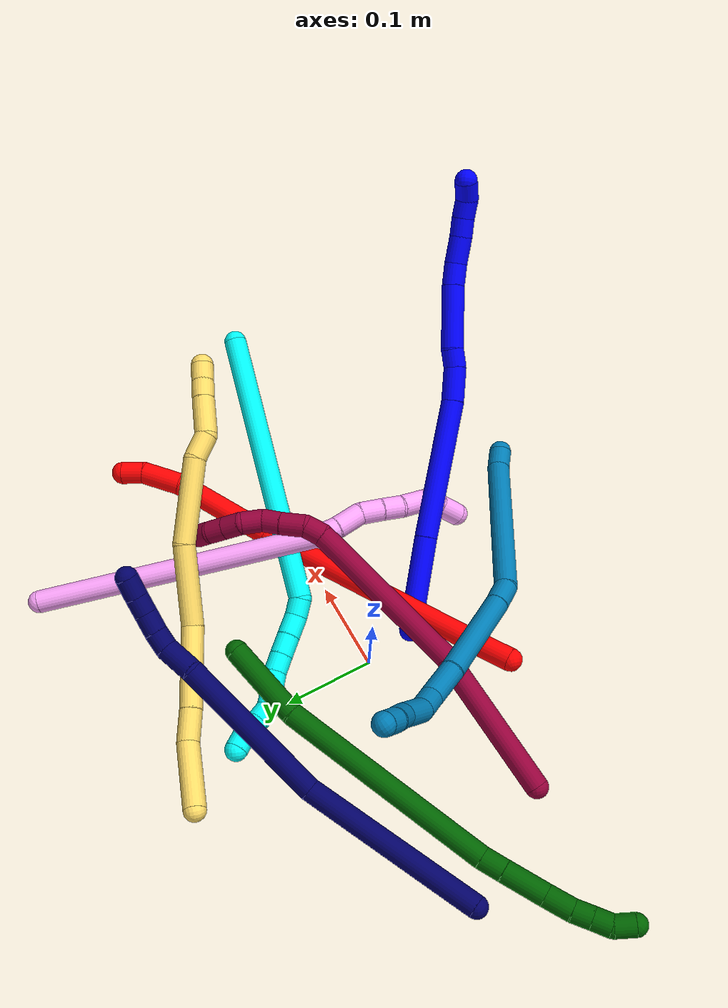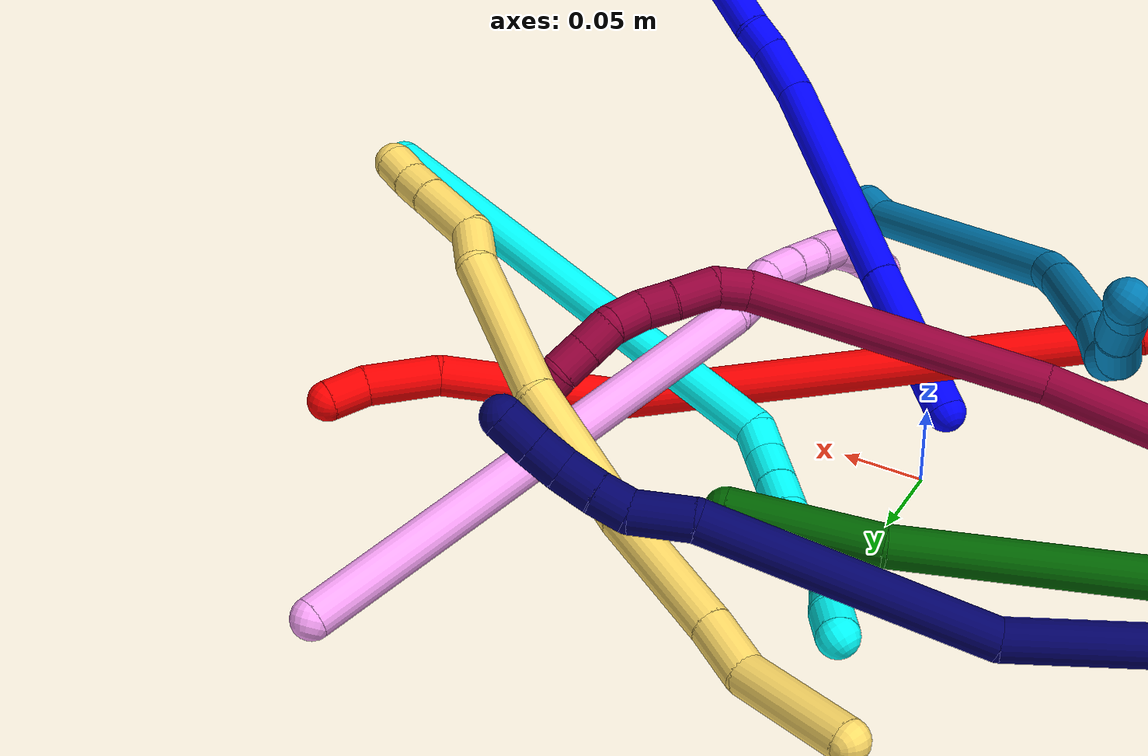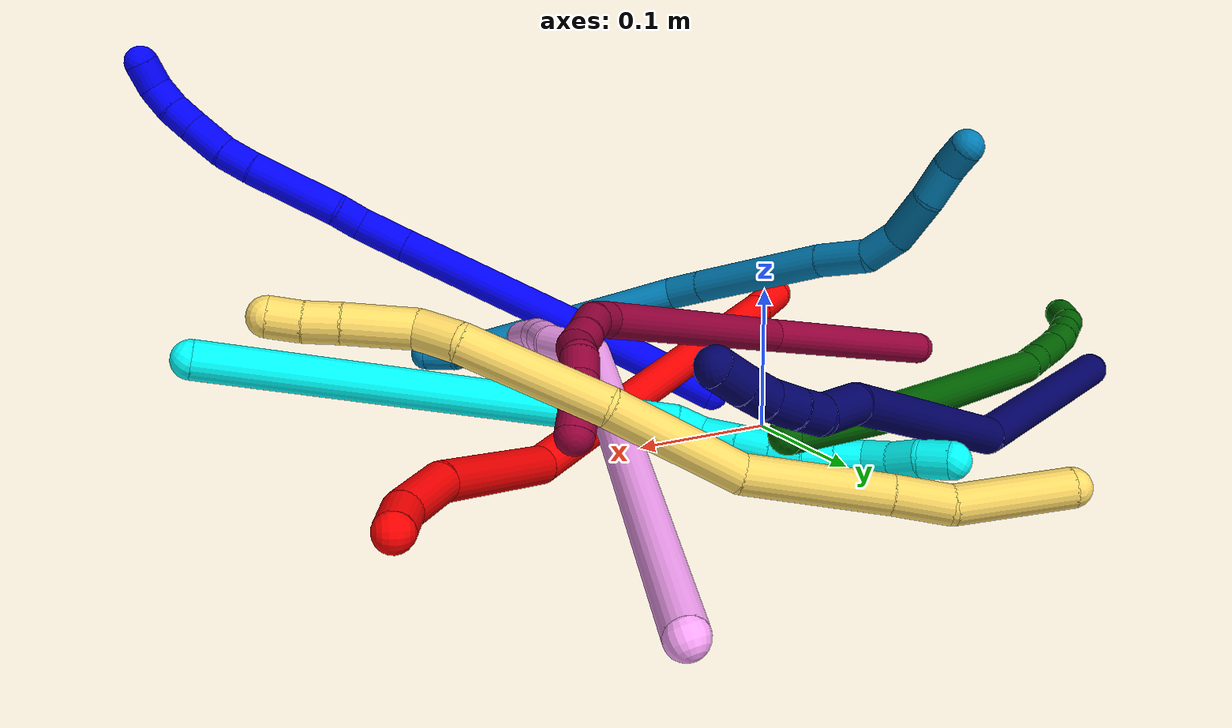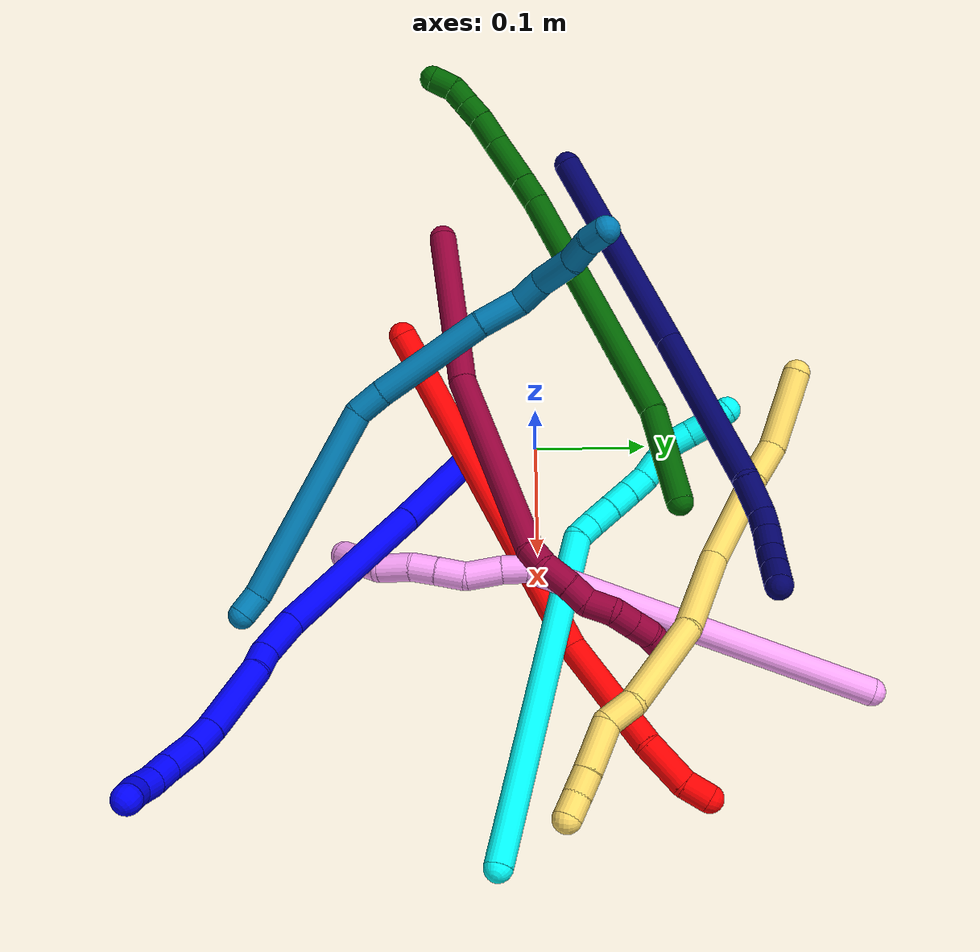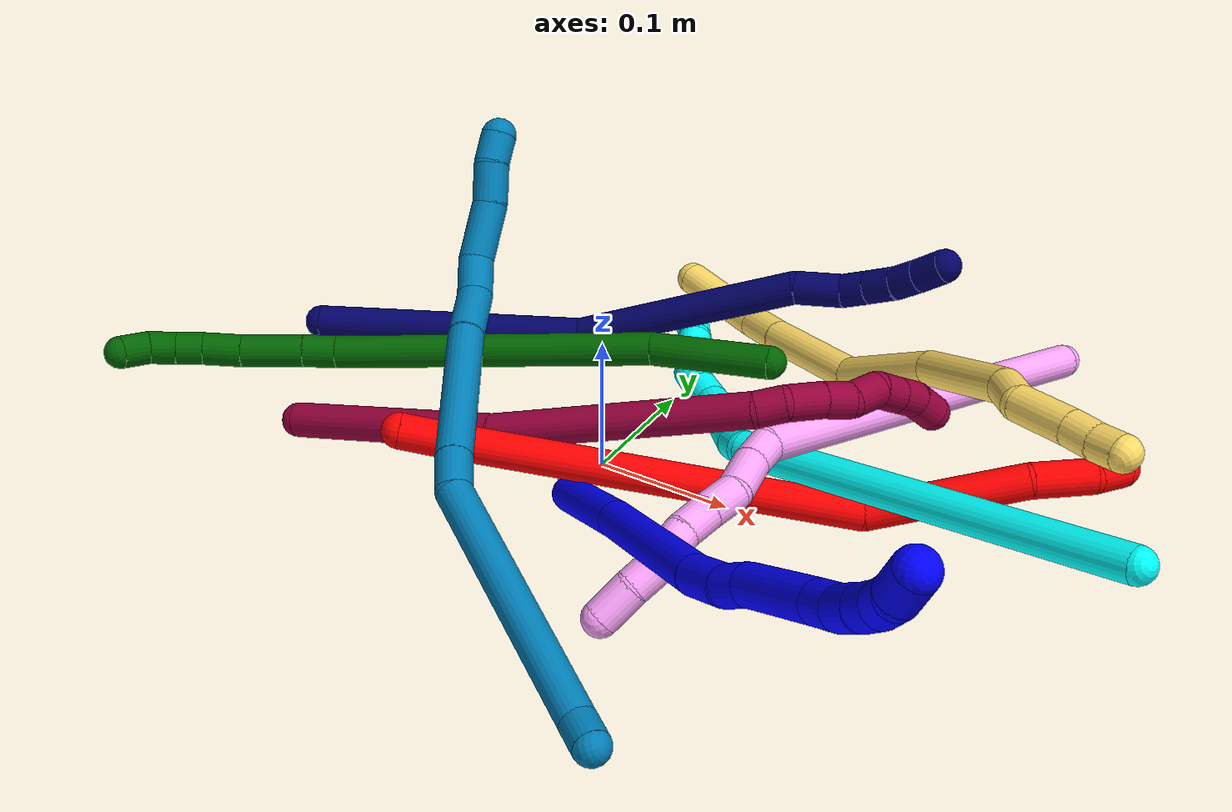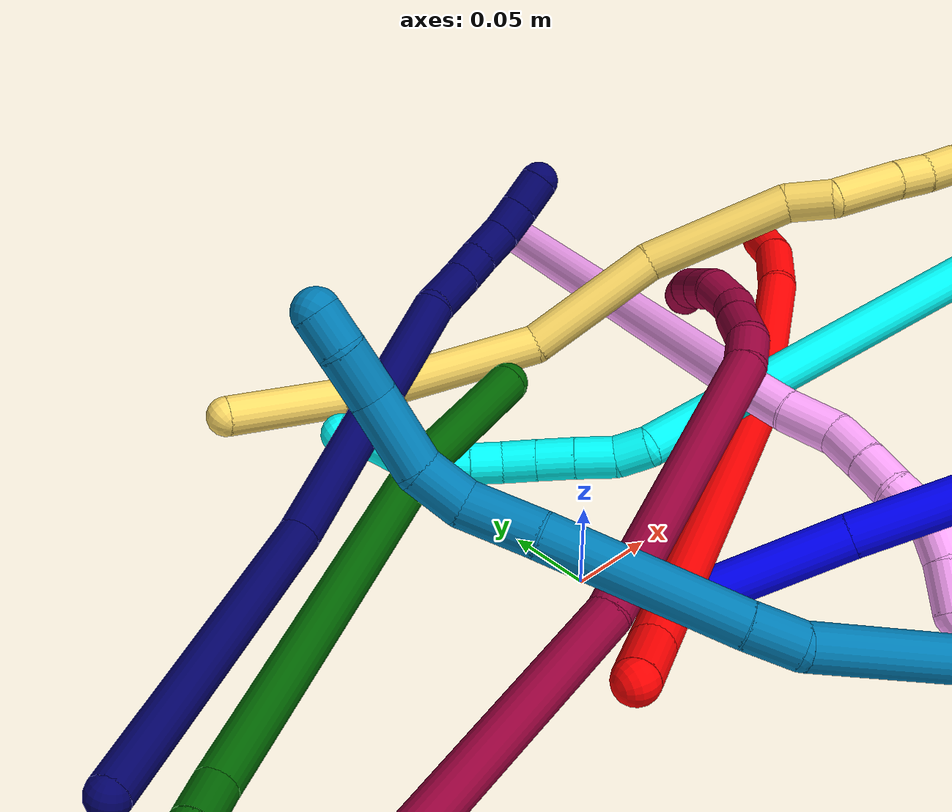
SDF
<sdf version="1.7">
 <world name="default">
  <plugin name="TubeGeneratorPlugin" filename="libtube_generator_plugin.so"/>
  <model name="photoneo_s_sensor">
   <static>1</static>
   <pose>0 0 2 1.57079 1.57079 3.14159</pose>
   <link name="link">
    <inertial><mass>0.1</mass></inertial>
    <sensor name="sensor" type="depth">
     <update_rate>30</update_rate>
     <camera>
      <horizontal_fov>1.22</horizontal_fov>
      <image><width>1920</width><height>1200</height><format>B8G8R8</format></image>
      <clip><near>0.1</near><far>4</far></clip>
      <depth_camera><output>points</output></depth_camera>
     </camera>
     <plugin name="camera_plugin" filename="libgazebo_ros_depth_camera.so">
      <baseline>0.2</baseline>
      <alwaysOn>1</alwaysOn>
      <updateRate>0.0</updateRate>
      <cameraName>camera_ir</cameraName>
      <imageTopicName>/camera/color/image_raw</imageTopicName>
      <cameraInfoTopicName>/camera/color/camera_info</cameraInfoTopicName>
      <depthImageTopicName>/camera/depth/image_raw</depthImageTopicName>
      <depthImageCameraInfoTopicName>/camera/depth/camera_info</depthImageCameraInfoTopicName>
      <pointCloudTopicName>/camera/depth/points</pointCloudTopicName>
      <frameName>fr_optical</frameName>
      <pointCloudCutoff>0.1</pointCloudCutoff>
      <pointCloudCutoffMax>2.0</pointCloudCutoffMax>
      <distortionK1>0</distortionK1>
      <distortionK2>0</distortionK2>
      <distortionK3>0</distortionK3>
      <distortionT1>0</distortionT1>
      <distortionT2>0</distortionT2>
      <CxPrime>0</CxPrime>
      <Cx>0</Cx>
      <Cy>0</Cy>
      <focalLength>0</focalLength>
      <hackBaseline>0</hackBaseline>
     </plugin>
    </sensor>
   </link>
  </model>
  <gravity>0 0 -9.8</gravity>
  <magnetic_field>6e-06 2.3e-05 -4.2e-05</magnetic_field>
  <atmosphere type="adiabatic"/>
  <physics name="default_physics" default="0" type="ode">
   <max_step_size>0.003</max_step_size>
   <real_time_factor>1</real_time_factor>
   <real_time_update_rate>1000</real_time_update_rate>
   <max_contacts>10000</max_contacts>
   <ode>
    <solver>
     <type>quick</type>
     <iters>100</iters>
     <sor>1.3</sor>
     <use_dynamic_moi_rescaling>0</use_dynamic_moi_rescaling>
    </solver>
    <constraints>
     <contact_max_correcting_vel>0</contact_max_correcting_vel>
     <contact_surface_layer>0.001</contact_surface_layer>
     <cfm>0</cfm>
     <erp>0.2</erp>
    </constraints>
   </ode>
  </physics>
  <scene><ambient>0.4 0.4 0.4 1</ambient><background>0.7 0.7 0.7 1</background><shadows>0</shadows></scene>
  <audio><device>default</device></audio>
  <spherical_coordinates>
   <surface_model>EARTH_WGS84</surface_model>
   <latitude_deg>0</latitude_deg>
   <longitude_deg>0</longitude_deg>
   <elevation>0</elevation>
   <heading_deg>0</heading_deg>
  </spherical_coordinates>
  <model name="bin">
   <static>1</static>
   <link name="bottom">
    <collision name="collision-bottom">
     <pose>0 0 -0.01 0 -0 0</pose>
     <geometry><box><size>0.8 0.6 0.02</size></box></geometry>
     <surface>
      <friction><ode><mu>100</mu><mu2>100</mu2></ode></friction>
      <contact><collide_bitmask>65535</collide_bitmask></contact>
     </surface>
    </collision>
   </link>
   <link name="west_wall">
    <collision name="collision-west_wall">
     <pose>-0.41 0 0.1 0 -0 0</pose>
     <geometry><box><size>0.02 0.6 0.2</size></box></geometry>
     <surface>
      <friction><ode><mu>100</mu><mu2>100</mu2></ode></friction>
      <contact><collide_bitmask>65535</collide_bitmask></contact>
     </surface>
    </collision>
   </link>
   <link name="east_wall">
    <collision name="collision-east_wall">
     <pose>0.41 0 0.1 0 -0 0</pose>
     <geometry><box><size>0.02 0.6 0.2</size></box></geometry>
     <surface>
      <friction><ode><mu>100</mu><mu2>100</mu2></ode></friction>
      <contact><collide_bitmask>65535</collide_bitmask></contact>
     </surface>
    </collision>
   </link>
   <link name="south_wall">
    <collision name="collision-south_wall">
     <pose>0 -0.31 0.1 0 -0 0</pose>
     <geometry><box><size>0.8 0.02 0.2</size></box></geometry>
     <surface>
      <friction><ode><mu>100</mu><mu2>100</mu2></ode></friction>
      <contact><collide_bitmask>65535</collide_bitmask></contact>
     </surface>
    </collision>
   </link>
   <link name="north_wall">
    <collision name="collision-north_wall">
     <pose>0 0.31 0.1 0 -0 0</pose>
     <geometry><box><size>0.8 0.02 0.2</size></box></geometry>
     <surface>
      <friction><ode><mu>100</mu><mu2>100</mu2></ode></friction>
      <contact><collide_bitmask>65535</collide_bitmask></contact>
     </surface>
    </collision>
   </link>
  </model>
  <model name="1">
   <static>0</static>
   <link name="1">
    <collision name="collision-cylinder-e_1_1_4">
     <pose>0.00173 -0.002735 0.051504 0.053059 0.033531 0.00089</pose>
     <geometry><cylinder><radius>0.0125</radius><length>0.103212</length></cylinder></geometry>
     <surface>
      <friction><ode><mu>1.16</mu><mu2>1.16</mu2><slip1>0</slip1><slip2>0</slip2></ode></friction>
      <contact><ode><kp>1e+06</kp><kd>1</kd><max_vel>0</max_vel><min_depth>0.001</min_depth></ode></contact>
     </surface>
    </collision>
    <visual name="visual-cylinder-e_1_1_4">
     <pose>0.00173 -0.002735 0.051504 0.053059 0.033531 0.00089</pose>
     <geometry><cylinder><radius>0.0125</radius><length>0.103212</length></cylinder></geometry>
     <material><ambient>0 0 1 1</ambient></material>
    </visual>
    <collision name="collision-cylinder-e_2_4_5">
     <pose>0.008549 -0.010688 0.179289 0.068293 0.066458 0.002271</pose>
     <geometry><cylinder><radius>0.0125</radius><length>0.153255</length></cylinder></geometry>
     <surface>
      <friction><ode><mu>1.16</mu><mu2>1.16</mu2><slip1>0</slip1><slip2>0</slip2></ode></friction>
      <contact><ode><kp>1e+06</kp><kd>1</kd><max_vel>0</max_vel><min_depth>0.001</min_depth></ode></contact>
     </surface>
    </collision>
    <visual name="visual-cylinder-e_2_4_5">
     <pose>0.008549 -0.010688 0.179289 0.068293 0.066458 0.002271</pose>
     <geometry><cylinder><radius>0.0125</radius><length>0.153255</length></cylinder></geometry>
     <material><ambient>0 0 1 1</ambient></material>
    </visual>
    <collision name="collision-cylinder-e_3_5_6">
     <pose>0.013115 -0.015431 0.274519 -0.025061 -0.02754 0.000345</pose>
     <geometry><cylinder><radius>0.0125</radius><length>0.037926</length></cylinder></geometry>
     <surface>
      <friction><ode><mu>1.16</mu><mu2>1.16</mu2><slip1>0</slip1><slip2>0</slip2></ode></friction>
      <contact><ode><kp>1e+06</kp><kd>1</kd><max_vel>0</max_vel><min_depth>0.001</min_depth></ode></contact>
     </surface>
    </collision>
    <visual name="visual-cylinder-e_3_5_6">
     <pose>0.013115 -0.015431 0.274519 -0.025061 -0.02754 0.000345</pose>
     <geometry><cylinder><radius>0.0125</radius><length>0.037926</length></cylinder></geometry>
     <material><ambient>0 0 1 1</ambient></material>
    </visual>
    <collision name="collision-cylinder-e_4_6_7">
     <pose>0.010023 -0.013274 0.303294 -0.169539 -0.252311 0.021553</pose>
     <geometry><cylinder><radius>0.0125</radius><length>0.020588</length></cylinder></geometry>
     <surface>
      <friction><ode><mu>1.16</mu><mu2>1.16</mu2><slip1>0</slip1><slip2>0</slip2></ode></friction>
      <contact><ode><kp>1e+06</kp><kd>1</kd><max_vel>0</max_vel><min_depth>0.001</min_depth></ode></contact>
     </surface>
    </collision>
    <visual name="visual-cylinder-e_4_6_7">
     <pose>0.010023 -0.013274 0.303294 -0.169539 -0.252311 0.021553</pose>
     <geometry><cylinder><radius>0.0125</radius><length>0.020588</length></cylinder></geometry>
     <material><ambient>0 0 1 1</ambient></material>
    </visual>
    <collision name="collision-cylinder-e_5_7_8">
     <pose>0.004982 -0.009287 0.347612 -0.066718 -0.071368 0.002383</pose>
     <geometry><cylinder><radius>0.0125</radius><length>0.069317</length></cylinder></geometry>
     <surface>
      <friction><ode><mu>1.16</mu><mu2>1.16</mu2><slip1>0</slip1><slip2>0</slip2></ode></friction>
      <contact><ode><kp>1e+06</kp><kd>1</kd><max_vel>0</max_vel><min_depth>0.001</min_depth></ode></contact>
     </surface>
    </collision>
    <visual name="visual-cylinder-e_5_7_8">
     <pose>0.004982 -0.009287 0.347612 -0.066718 -0.071368 0.002383</pose>
     <geometry><cylinder><radius>0.0125</radius><length>0.069317</length></cylinder></geometry>
     <material><ambient>0 0 1 1</ambient></material>
    </visual>
    <collision name="collision-cylinder-e_6_8_9">
     <pose>0.001775 -0.007446 0.394254 0.038176 -0.06044 -0.001154</pose>
     <geometry><cylinder><radius>0.0125</radius><length>0.024358</length></cylinder></geometry>
     <surface>
      <friction><ode><mu>1.16</mu><mu2>1.16</mu2><slip1>0</slip1><slip2>0</slip2></ode></friction>
      <contact><ode><kp>1e+06</kp><kd>1</kd><max_vel>0</max_vel><min_depth>0.001</min_depth></ode></contact>
     </surface>
    </collision>
    <visual name="visual-cylinder-e_6_8_9">
     <pose>0.001775 -0.007446 0.394254 0.038176 -0.06044 -0.001154</pose>
     <geometry><cylinder><radius>0.0125</radius><length>0.024358</length></cylinder></geometry>
     <material><ambient>0 0 1 1</ambient></material>
    </visual>
    <collision name="collision-cylinder-e_7_9_10">
     <pose>-0.001524 -0.010424 0.420783 0.173049 -0.173799 -0.015113</pose>
     <geometry><cylinder><radius>0.0125</radius><length>0.029646</length></cylinder></geometry>
     <surface>
      <friction><ode><mu>1.16</mu><mu2>1.16</mu2><slip1>0</slip1><slip2>0</slip2></ode></friction>
      <contact><ode><kp>1e+06</kp><kd>1</kd><max_vel>0</max_vel><min_depth>0.001</min_depth></ode></contact>
     </surface>
    </collision>
    <visual name="visual-cylinder-e_7_9_10">
     <pose>-0.001524 -0.010424 0.420783 0.173049 -0.173799 -0.015113</pose>
     <geometry><cylinder><radius>0.0125</radius><length>0.029646</length></cylinder></geometry>
     <material><ambient>0 0 1 1</ambient></material>
    </visual>
    <collision name="collision-cylinder-e_8_10_11">
     <pose>-0.006675 -0.014233 0.44502 0.130639 -0.254739 -0.016753</pose>
     <geometry><cylinder><radius>0.0125</radius><length>0.020544</length></cylinder></geometry>
     <surface>
      <friction><ode><mu>1.16</mu><mu2>1.16</mu2><slip1>0</slip1><slip2>0</slip2></ode></friction>
      <contact><ode><kp>1e+06</kp><kd>1</kd><max_vel>0</max_vel><min_depth>0.001</min_depth></ode></contact>
     </surface>
    </collision>
    <visual name="visual-cylinder-e_8_10_11">
     <pose>-0.006675 -0.014233 0.44502 0.130639 -0.254739 -0.016753</pose>
     <geometry><cylinder><radius>0.0125</radius><length>0.020544</length></cylinder></geometry>
     <material><ambient>0 0 1 1</ambient></material>
    </visual>
    <collision name="collision-cylinder-e_9_11_12">
     <pose>-0.012581 -0.018117 0.464093 0.273859 -0.333478 -0.046373</pose>
     <geometry><cylinder><radius>0.0125</radius><length>0.020265</length></cylinder></geometry>
     <surface>
      <friction><ode><mu>1.16</mu><mu2>1.16</mu2><slip1>0</slip1><slip2>0</slip2></ode></friction>
      <contact><ode><kp>1e+06</kp><kd>1</kd><max_vel>0</max_vel><min_depth>0.001</min_depth></ode></contact>
     </surface>
    </collision>
    <visual name="visual-cylinder-e_9_11_12">
     <pose>-0.012581 -0.018117 0.464093 0.273859 -0.333478 -0.046373</pose>
     <geometry><cylinder><radius>0.0125</radius><length>0.020265</length></cylinder></geometry>
     <material><ambient>0 0 1 1</ambient></material>
    </visual>
    <collision name="collision-cylinder-e_10_12_2">
     <pose>-0.022874 -0.022048 0.480967 0.173458 -0.731496 -0.066573</pose>
     <geometry><cylinder><radius>0.0125</radius><length>0.02089</length></cylinder></geometry>
     <surface>
      <friction><ode><mu>1.16</mu><mu2>1.16</mu2><slip1>0</slip1><slip2>0</slip2></ode></friction>
      <contact><ode><kp>1e+06</kp><kd>1</kd><max_vel>0</max_vel><min_depth>0.001</min_depth></ode></contact>
     </surface>
    </collision>
    <visual name="visual-cylinder-e_10_12_2">
     <pose>-0.022874 -0.022048 0.480967 0.173458 -0.731496 -0.066573</pose>
     <geometry><cylinder><radius>0.0125</radius><length>0.02089</length></cylinder></geometry>
     <material><ambient>0 0 1 1</ambient></material>
    </visual>
    <collision name="collision-sphere-2">
     <pose>-0.029851 -0.023389 0.488623 0 -0 0</pose>
     <geometry><sphere><radius>0.0125</radius></sphere></geometry>
     <surface>
      <friction><ode><mu>1.16</mu><mu2>1.16</mu2><slip1>0</slip1><slip2>0</slip2></ode></friction>
      <contact><ode><kp>1e+06</kp><kd>1</kd><max_vel>0</max_vel><min_depth>0.001</min_depth></ode></contact>
     </surface>
    </collision>
    <visual name="visual-sphere-2">
     <pose>-0.029851 -0.023389 0.488623 0 -0 0</pose>
     <geometry><sphere><radius>0.0125</radius></sphere></geometry>
     <material><ambient>0 0 1 1</ambient></material>
    </visual>
    <collision name="collision-sphere-12">
     <pose>-0.015897 -0.020706 0.473311 0 -0 0</pose>
     <geometry><sphere><radius>0.0125</radius></sphere></geometry>
     <surface>
      <friction><ode><mu>1.16</mu><mu2>1.16</mu2><slip1>0</slip1><slip2>0</slip2></ode></friction>
      <contact><ode><kp>1e+06</kp><kd>1</kd><max_vel>0</max_vel><min_depth>0.001</min_depth></ode></contact>
     </surface>
    </collision>
    <visual name="visual-sphere-12">
     <pose>-0.015897 -0.020706 0.473311 0 -0 0</pose>
     <geometry><sphere><radius>0.0125</radius></sphere></geometry>
     <material><ambient>0 0 1 1</ambient></material>
    </visual>
    <collision name="collision-sphere-11">
     <pose>-0.009264 -0.015528 0.454876 0 -0 0</pose>
     <geometry><sphere><radius>0.0125</radius></sphere></geometry>
     <surface>
      <friction><ode><mu>1.16</mu><mu2>1.16</mu2><slip1>0</slip1><slip2>0</slip2></ode></friction>
      <contact><ode><kp>1e+06</kp><kd>1</kd><max_vel>0</max_vel><min_depth>0.001</min_depth></ode></contact>
     </surface>
    </collision>
    <visual name="visual-sphere-11">
     <pose>-0.009264 -0.015528 0.454876 0 -0 0</pose>
     <geometry><sphere><radius>0.0125</radius></sphere></geometry>
     <material><ambient>0 0 1 1</ambient></material>
    </visual>
    <collision name="collision-sphere-10">
     <pose>-0.004087 -0.012938 0.435165 0 -0 0</pose>
     <geometry><sphere><radius>0.0125</radius></sphere></geometry>
     <surface>
      <friction><ode><mu>1.16</mu><mu2>1.16</mu2><slip1>0</slip1><slip2>0</slip2></ode></friction>
      <contact><ode><kp>1e+06</kp><kd>1</kd><max_vel>0</max_vel><min_depth>0.001</min_depth></ode></contact>
     </surface>
    </collision>
    <visual name="visual-sphere-10">
     <pose>-0.004087 -0.012938 0.435165 0 -0 0</pose>
     <geometry><sphere><radius>0.0125</radius></sphere></geometry>
     <material><ambient>0 0 1 1</ambient></material>
    </visual>
    <collision name="collision-sphere-9">
     <pose>0.001039 -0.00791 0.406402 0 -0 0</pose>
     <geometry><sphere><radius>0.0125</radius></sphere></geometry>
     <surface>
      <friction><ode><mu>1.16</mu><mu2>1.16</mu2><slip1>0</slip1><slip2>0</slip2></ode></friction>
      <contact><ode><kp>1e+06</kp><kd>1</kd><max_vel>0</max_vel><min_depth>0.001</min_depth></ode></contact>
     </surface>
    </collision>
    <visual name="visual-sphere-9">
     <pose>0.001039 -0.00791 0.406402 0 -0 0</pose>
     <geometry><sphere><radius>0.0125</radius></sphere></geometry>
     <material><ambient>0 0 1 1</ambient></material>
    </visual>
    <collision name="collision-sphere-4">
     <pose>0.00346 -0.005471 0.103008 0 -0 0</pose>
     <geometry><sphere><radius>0.0125</radius></sphere></geometry>
     <surface>
      <friction><ode><mu>1.16</mu><mu2>1.16</mu2><slip1>0</slip1><slip2>0</slip2></ode></friction>
      <contact><ode><kp>1e+06</kp><kd>1</kd><max_vel>0</max_vel><min_depth>0.001</min_depth></ode></contact>
     </surface>
    </collision>
    <visual name="visual-sphere-4">
     <pose>0.00346 -0.005471 0.103008 0 -0 0</pose>
     <geometry><sphere><radius>0.0125</radius></sphere></geometry>
     <material><ambient>0 0 1 1</ambient></material>
    </visual>
    <collision name="collision-sphere-1">
     <geometry><sphere><radius>0.0125</radius></sphere></geometry>
     <surface>
      <friction><ode><mu>1.16</mu><mu2>1.16</mu2><slip1>0</slip1><slip2>0</slip2></ode></friction>
      <contact><ode><kp>1e+06</kp><kd>1</kd><max_vel>0</max_vel><min_depth>0.001</min_depth></ode></contact>
     </surface>
    </collision>
    <visual name="visual-sphere-1">
     <geometry><sphere><radius>0.0125</radius></sphere></geometry>
     <material><ambient>0 0 1 1</ambient></material>
    </visual>
    <collision name="collision-sphere-8">
     <pose>0.002511 -0.006982 0.382106 0 -0 0</pose>
     <geometry><sphere><radius>0.0125</radius></sphere></geometry>
     <surface>
      <friction><ode><mu>1.16</mu><mu2>1.16</mu2><slip1>0</slip1><slip2>0</slip2></ode></friction>
      <contact><ode><kp>1e+06</kp><kd>1</kd><max_vel>0</max_vel><min_depth>0.001</min_depth></ode></contact>
     </surface>
    </collision>
    <visual name="visual-sphere-8">
     <pose>0.002511 -0.006982 0.382106 0 -0 0</pose>
     <geometry><sphere><radius>0.0125</radius></sphere></geometry>
     <material><ambient>0 0 1 1</ambient></material>
    </visual>
    <collision name="collision-sphere-5">
     <pose>0.013638 -0.015906 0.255569 0 -0 0</pose>
     <geometry><sphere><radius>0.0125</radius></sphere></geometry>
     <surface>
      <friction><ode><mu>1.16</mu><mu2>1.16</mu2><slip1>0</slip1><slip2>0</slip2></ode></friction>
      <contact><ode><kp>1e+06</kp><kd>1</kd><max_vel>0</max_vel><min_depth>0.001</min_depth></ode></contact>
     </surface>
    </collision>
    <visual name="visual-sphere-5">
     <pose>0.013638 -0.015906 0.255569 0 -0 0</pose>
     <geometry><sphere><radius>0.0125</radius></sphere></geometry>
     <material><ambient>0 0 1 1</ambient></material>
    </visual>
    <collision name="collision-sphere-6">
     <pose>0.012593 -0.014956 0.293469 0 -0 0</pose>
     <geometry><sphere><radius>0.0125</radius></sphere></geometry>
     <surface>
      <friction><ode><mu>1.16</mu><mu2>1.16</mu2><slip1>0</slip1><slip2>0</slip2></ode></friction>
      <contact><ode><kp>1e+06</kp><kd>1</kd><max_vel>0</max_vel><min_depth>0.001</min_depth></ode></contact>
     </surface>
    </collision>
    <visual name="visual-sphere-6">
     <pose>0.012593 -0.014956 0.293469 0 -0 0</pose>
     <geometry><sphere><radius>0.0125</radius></sphere></geometry>
     <material><ambient>0 0 1 1</ambient></material>
    </visual>
    <collision name="collision-sphere-7">
     <pose>0.007454 -0.011592 0.313119 0 -0 0</pose>
     <geometry><sphere><radius>0.0125</radius></sphere></geometry>
     <surface>
      <friction><ode><mu>1.16</mu><mu2>1.16</mu2><slip1>0</slip1><slip2>0</slip2></ode></friction>
      <contact><ode><kp>1e+06</kp><kd>1</kd><max_vel>0</max_vel><min_depth>0.001</min_depth></ode></contact>
     </surface>
    </collision>
    <visual name="visual-sphere-7">
     <pose>0.007454 -0.011592 0.313119 0 -0 0</pose>
     <geometry><sphere><radius>0.0125</radius></sphere></geometry>
     <material><ambient>0 0 1 1</ambient></material>
    </visual>
    <inertial>
     <pose>0.003332 -0.010066 0.248432 0 -0 0</pose>
     <mass>0.5</mass>
     <inertia>
      <ixx>0.000447</ixx>
      <ixy>0</ixy>
      <ixz>0</ixz>
      <iyy>0.000447</iyy>
      <iyz>0</iyz>
      <izz>4.5e-05</izz>
     </inertia>
    </inertial>
   </link>
   <pose>0.008562 -0.056091 0.011502 -0.739301 0.960977 -1.45186</pose>
  </model>
  <model name="2">
   <static>0</static>
   <link name="2">
    <collision name="collision-cylinder-e_1_1_4">
     <pose>0.002633 0.010689 -0.011846 -2.40747 0.163574 -0.420098</pose>
     <geometry><cylinder><radius>0.0125</radius><length>0.032343</length></cylinder></geometry>
     <surface>
      <friction><ode><mu>1.16</mu><mu2>1.16</mu2><slip1>0</slip1><slip2>0</slip2></ode></friction>
      <contact><ode><kp>1e+06</kp><kd>1</kd><max_vel>0</max_vel><min_depth>0.001</min_depth></ode></contact>
     </surface>
    </collision>
    <visual name="visual-cylinder-e_1_1_4">
     <pose>0.002633 0.010689 -0.011846 -2.40747 0.163574 -0.420098</pose>
     <geometry><cylinder><radius>0.0125</radius><length>0.032343</length></cylinder></geometry>
     <material><ambient>1 0 0 1</ambient></material>
    </visual>
    <collision name="collision-cylinder-e_2_4_5">
     <pose>0.032022 0.112243 -0.130175 -2.43517 0.188852 -0.502904</pose>
     <geometry><cylinder><radius>0.0125</radius><length>0.285033</length></cylinder></geometry>
     <surface>
      <friction><ode><mu>1.16</mu><mu2>1.16</mu2><slip1>0</slip1><slip2>0</slip2></ode></friction>
      <contact><ode><kp>1e+06</kp><kd>1</kd><max_vel>0</max_vel><min_depth>0.001</min_depth></ode></contact>
     </surface>
    </collision>
    <visual name="visual-cylinder-e_2_4_5">
     <pose>0.032022 0.112243 -0.130175 -2.43517 0.188852 -0.502904</pose>
     <geometry><cylinder><radius>0.0125</radius><length>0.285033</length></cylinder></geometry>
     <material><ambient>1 0 0 1</ambient></material>
    </visual>
    <collision name="collision-cylinder-e_3_5_6">
     <pose>0.089113 0.230544 -0.275376 -2.52511 0.568809 -1.4855</pose>
     <geometry><cylinder><radius>0.0125</radius><length>0.112642</length></cylinder></geometry>
     <surface>
      <friction><ode><mu>1.16</mu><mu2>1.16</mu2><slip1>0</slip1><slip2>0</slip2></ode></friction>
      <contact><ode><kp>1e+06</kp><kd>1</kd><max_vel>0</max_vel><min_depth>0.001</min_depth></ode></contact>
     </surface>
    </collision>
    <visual name="visual-cylinder-e_3_5_6">
     <pose>0.089113 0.230544 -0.275376 -2.52511 0.568809 -1.4855</pose>
     <geometry><cylinder><radius>0.0125</radius><length>0.112642</length></cylinder></geometry>
     <material><ambient>1 0 0 1</ambient></material>
    </visual>
    <collision name="collision-cylinder-e_4_6_7">
     <pose>0.128417 0.273739 -0.327447 -2.27374 0.409624 -0.842849</pose>
     <geometry><cylinder><radius>0.0125</radius><length>0.045037</length></cylinder></geometry>
     <surface>
      <friction><ode><mu>1.16</mu><mu2>1.16</mu2><slip1>0</slip1><slip2>0</slip2></ode></friction>
      <contact><ode><kp>1e+06</kp><kd>1</kd><max_vel>0</max_vel><min_depth>0.001</min_depth></ode></contact>
     </surface>
    </collision>
    <visual name="visual-cylinder-e_4_6_7">
     <pose>0.128417 0.273739 -0.327447 -2.27374 0.409624 -0.842849</pose>
     <geometry><cylinder><radius>0.0125</radius><length>0.045037</length></cylinder></geometry>
     <material><ambient>1 0 0 1</ambient></material>
    </visual>
    <collision name="collision-cylinder-e_5_7_2">
     <pose>0.142788 0.300036 -0.344715 -1.92644 0.448019 -0.633286</pose>
     <geometry><cylinder><radius>0.0125</radius><length>0.024945</length></cylinder></geometry>
     <surface>
      <friction><ode><mu>1.16</mu><mu2>1.16</mu2><slip1>0</slip1><slip2>0</slip2></ode></friction>
      <contact><ode><kp>1e+06</kp><kd>1</kd><max_vel>0</max_vel><min_depth>0.001</min_depth></ode></contact>
     </surface>
    </collision>
    <visual name="visual-cylinder-e_5_7_2">
     <pose>0.142788 0.300036 -0.344715 -1.92644 0.448019 -0.633286</pose>
     <geometry><cylinder><radius>0.0125</radius><length>0.024945</length></cylinder></geometry>
     <material><ambient>1 0 0 1</ambient></material>
    </visual>
    <collision name="collision-sphere-2">
     <pose>0.148191 0.310573 -0.348629 0 -0 0</pose>
     <geometry><sphere><radius>0.0125</radius></sphere></geometry>
     <surface>
      <friction><ode><mu>1.16</mu><mu2>1.16</mu2><slip1>0</slip1><slip2>0</slip2></ode></friction>
      <contact><ode><kp>1e+06</kp><kd>1</kd><max_vel>0</max_vel><min_depth>0.001</min_depth></ode></contact>
     </surface>
    </collision>
    <visual name="visual-sphere-2">
     <pose>0.148191 0.310573 -0.348629 0 -0 0</pose>
     <geometry><sphere><radius>0.0125</radius></sphere></geometry>
     <material><ambient>1 0 0 1</ambient></material>
    </visual>
    <collision name="collision-sphere-7">
     <pose>0.137385 0.289498 -0.3408 0 -0 0</pose>
     <geometry><sphere><radius>0.0125</radius></sphere></geometry>
     <surface>
      <friction><ode><mu>1.16</mu><mu2>1.16</mu2><slip1>0</slip1><slip2>0</slip2></ode></friction>
      <contact><ode><kp>1e+06</kp><kd>1</kd><max_vel>0</max_vel><min_depth>0.001</min_depth></ode></contact>
     </surface>
    </collision>
    <visual name="visual-sphere-7">
     <pose>0.137385 0.289498 -0.3408 0 -0 0</pose>
     <geometry><sphere><radius>0.0125</radius></sphere></geometry>
     <material><ambient>1 0 0 1</ambient></material>
    </visual>
    <collision name="collision-sphere-6">
     <pose>0.119449 0.25798 -0.314094 0 -0 0</pose>
     <geometry><sphere><radius>0.0125</radius></sphere></geometry>
     <surface>
      <friction><ode><mu>1.16</mu><mu2>1.16</mu2><slip1>0</slip1><slip2>0</slip2></ode></friction>
      <contact><ode><kp>1e+06</kp><kd>1</kd><max_vel>0</max_vel><min_depth>0.001</min_depth></ode></contact>
     </surface>
    </collision>
    <visual name="visual-sphere-6">
     <pose>0.119449 0.25798 -0.314094 0 -0 0</pose>
     <geometry><sphere><radius>0.0125</radius></sphere></geometry>
     <material><ambient>1 0 0 1</ambient></material>
    </visual>
    <collision name="collision-sphere-5">
     <pose>0.058776 0.203108 -0.236659 0 -0 0</pose>
     <geometry><sphere><radius>0.0125</radius></sphere></geometry>
     <surface>
      <friction><ode><mu>1.16</mu><mu2>1.16</mu2><slip1>0</slip1><slip2>0</slip2></ode></friction>
      <contact><ode><kp>1e+06</kp><kd>1</kd><max_vel>0</max_vel><min_depth>0.001</min_depth></ode></contact>
     </surface>
    </collision>
    <visual name="visual-sphere-5">
     <pose>0.058776 0.203108 -0.236659 0 -0 0</pose>
     <geometry><sphere><radius>0.0125</radius></sphere></geometry>
     <material><ambient>1 0 0 1</ambient></material>
    </visual>
    <collision name="collision-sphere-1">
     <geometry><sphere><radius>0.0125</radius></sphere></geometry>
     <surface>
      <friction><ode><mu>1.16</mu><mu2>1.16</mu2><slip1>0</slip1><slip2>0</slip2></ode></friction>
      <contact><ode><kp>1e+06</kp><kd>1</kd><max_vel>0</max_vel><min_depth>0.001</min_depth></ode></contact>
     </surface>
    </collision>
    <visual name="visual-sphere-1">
     <geometry><sphere><radius>0.0125</radius></sphere></geometry>
     <material><ambient>1 0 0 1</ambient></material>
    </visual>
    <collision name="collision-sphere-4">
     <pose>0.005267 0.021379 -0.023692 0 -0 0</pose>
     <geometry><sphere><radius>0.0125</radius></sphere></geometry>
     <surface>
      <friction><ode><mu>1.16</mu><mu2>1.16</mu2><slip1>0</slip1><slip2>0</slip2></ode></friction>
      <contact><ode><kp>1e+06</kp><kd>1</kd><max_vel>0</max_vel><min_depth>0.001</min_depth></ode></contact>
     </surface>
    </collision>
    <visual name="visual-sphere-4">
     <pose>0.005267 0.021379 -0.023692 0 -0 0</pose>
     <geometry><sphere><radius>0.0125</radius></sphere></geometry>
     <material><ambient>1 0 0 1</ambient></material>
    </visual>
    <inertial>
     <pose>0.057191 0.156241 -0.183705 0 -0 0</pose>
     <mass>0.5</mass>
     <inertia>
      <ixx>0.00067</ixx>
      <ixy>0</ixy>
      <ixz>0</ixz>
      <iyy>-0.002162</iyy>
      <iyz>0</iyz>
      <izz>-0.001772</izz>
     </inertia>
    </inertial>
   </link>
   <pose>-0.08799 -0.117197 0.063891 -1.65905 -0.981197 1.42974</pose>
  </model>
  <model name="3">
   <static>0</static>
   <link name="3">
    <collision name="collision-cylinder-e_1_1_4">
     <pose>-0.054862 -0.023895 -0.143656 2.97677 -0.360277 -2.28997</pose>
     <geometry><cylinder><radius>0.0125</radius><length>0.311242</length></cylinder></geometry>
     <surface>
      <friction><ode><mu>1.16</mu><mu2>1.16</mu2><slip1>0</slip1><slip2>0</slip2></ode></friction>
      <contact><ode><kp>1e+06</kp><kd>1</kd><max_vel>0</max_vel><min_depth>0.001</min_depth></ode></contact>
     </surface>
    </collision>
    <visual name="visual-cylinder-e_1_1_4">
     <pose>-0.054862 -0.023895 -0.143656 2.97677 -0.360277 -2.28997</pose>
     <geometry><cylinder><radius>0.0125</radius><length>0.311242</length></cylinder></geometry>
     <material><ambient>0.003922 1 0.996078 1</ambient></material>
    </visual>
    <collision name="collision-cylinder-e_2_4_5">
     <pose>-0.111621 -0.044523 -0.296667 -2.80565 -0.189295 1.02074</pose>
     <geometry><cylinder><radius>0.0125</radius><length>0.020176</length></cylinder></geometry>
     <surface>
      <friction><ode><mu>1.16</mu><mu2>1.16</mu2><slip1>0</slip1><slip2>0</slip2></ode></friction>
      <contact><ode><kp>1e+06</kp><kd>1</kd><max_vel>0</max_vel><min_depth>0.001</min_depth></ode></contact>
     </surface>
    </collision>
    <visual name="visual-cylinder-e_2_4_5">
     <pose>-0.111621 -0.044523 -0.296667 -2.80565 -0.189295 1.02074</pose>
     <geometry><cylinder><radius>0.0125</radius><length>0.020176</length></cylinder></geometry>
     <material><ambient>0.003922 1 0.996078 1</ambient></material>
    </visual>
    <collision name="collision-cylinder-e_3_5_6">
     <pose>-0.118773 -0.036145 -0.315694 -2.65542 -0.447612 1.48518</pose>
     <geometry><cylinder><radius>0.0125</radius><length>0.024273</length></cylinder></geometry>
     <surface>
      <friction><ode><mu>1.16</mu><mu2>1.16</mu2><slip1>0</slip1><slip2>0</slip2></ode></friction>
      <contact><ode><kp>1e+06</kp><kd>1</kd><max_vel>0</max_vel><min_depth>0.001</min_depth></ode></contact>
     </surface>
    </collision>
    <visual name="visual-cylinder-e_3_5_6">
     <pose>-0.118773 -0.036145 -0.315694 -2.65542 -0.447612 1.48518</pose>
     <geometry><cylinder><radius>0.0125</radius><length>0.024273</length></cylinder></geometry>
     <material><ambient>0.003922 1 0.996078 1</ambient></material>
    </visual>
    <collision name="collision-cylinder-e_4_6_7">
     <pose>-0.128662 -0.026292 -0.334617 -2.66801 -0.419621 1.44603</pose>
     <geometry><cylinder><radius>0.0125</radius><length>0.022761</length></cylinder></geometry>
     <surface>
      <friction><ode><mu>1.16</mu><mu2>1.16</mu2><slip1>0</slip1><slip2>0</slip2></ode></friction>
      <contact><ode><kp>1e+06</kp><kd>1</kd><max_vel>0</max_vel><min_depth>0.001</min_depth></ode></contact>
     </surface>
    </collision>
    <visual name="visual-cylinder-e_4_6_7">
     <pose>-0.128662 -0.026292 -0.334617 -2.66801 -0.419621 1.44603</pose>
     <geometry><cylinder><radius>0.0125</radius><length>0.022761</length></cylinder></geometry>
     <material><ambient>0.003922 1 0.996078 1</ambient></material>
    </visual>
    <collision name="collision-cylinder-e_5_7_8">
     <pose>-0.137583 -0.017312 -0.352456 -2.68306 -0.420573 1.48165</pose>
     <geometry><cylinder><radius>0.0125</radius><length>0.020989</length></cylinder></geometry>
     <surface>
      <friction><ode><mu>1.16</mu><mu2>1.16</mu2><slip1>0</slip1><slip2>0</slip2></ode></friction>
      <contact><ode><kp>1e+06</kp><kd>1</kd><max_vel>0</max_vel><min_depth>0.001</min_depth></ode></contact>
     </surface>
    </collision>
    <visual name="visual-cylinder-e_5_7_8">
     <pose>-0.137583 -0.017312 -0.352456 -2.68306 -0.420573 1.48165</pose>
     <geometry><cylinder><radius>0.0125</radius><length>0.020989</length></cylinder></geometry>
     <material><ambient>0.003922 1 0.996078 1</ambient></material>
    </visual>
    <collision name="collision-cylinder-e_6_8_9">
     <pose>-0.147637 -0.010737 -0.369075 -2.85857 -0.603975 2.28375</pose>
     <geometry><cylinder><radius>0.0125</radius><length>0.020315</length></cylinder></geometry>
     <surface>
      <friction><ode><mu>1.16</mu><mu2>1.16</mu2><slip1>0</slip1><slip2>0</slip2></ode></friction>
      <contact><ode><kp>1e+06</kp><kd>1</kd><max_vel>0</max_vel><min_depth>0.001</min_depth></ode></contact>
     </surface>
    </collision>
    <visual name="visual-cylinder-e_6_8_9">
     <pose>-0.147637 -0.010737 -0.369075 -2.85857 -0.603975 2.28375</pose>
     <geometry><cylinder><radius>0.0125</radius><length>0.020315</length></cylinder></geometry>
     <material><ambient>0.003922 1 0.996078 1</ambient></material>
    </visual>
    <collision name="collision-cylinder-e_7_9_10">
     <pose>-0.159035 -0.00587 -0.385058 -2.8334 -0.593318 2.20132</pose>
     <geometry><cylinder><radius>0.0125</radius><length>0.020139</length></cylinder></geometry>
     <surface>
      <friction><ode><mu>1.16</mu><mu2>1.16</mu2><slip1>0</slip1><slip2>0</slip2></ode></friction>
      <contact><ode><kp>1e+06</kp><kd>1</kd><max_vel>0</max_vel><min_depth>0.001</min_depth></ode></contact>
     </surface>
    </collision>
    <visual name="visual-cylinder-e_7_9_10">
     <pose>-0.159035 -0.00587 -0.385058 -2.8334 -0.593318 2.20132</pose>
     <geometry><cylinder><radius>0.0125</radius><length>0.020139</length></cylinder></geometry>
     <material><ambient>0.003922 1 0.996078 1</ambient></material>
    </visual>
    <collision name="collision-cylinder-e_8_10_11">
     <pose>-0.170164 0.002962 -0.39853 -2.29012 -0.581055 1.16581</pose>
     <geometry><cylinder><radius>0.0125</radius><length>0.020036</length></cylinder></geometry>
     <surface>
      <friction><ode><mu>1.16</mu><mu2>1.16</mu2><slip1>0</slip1><slip2>0</slip2></ode></friction>
      <contact><ode><kp>1e+06</kp><kd>1</kd><max_vel>0</max_vel><min_depth>0.001</min_depth></ode></contact>
     </surface>
    </collision>
    <visual name="visual-cylinder-e_8_10_11">
     <pose>-0.170164 0.002962 -0.39853 -2.29012 -0.581055 1.16581</pose>
     <geometry><cylinder><radius>0.0125</radius><length>0.020036</length></cylinder></geometry>
     <material><ambient>0.003922 1 0.996078 1</ambient></material>
    </visual>
    <collision name="collision-cylinder-e_9_11_12">
     <pose>-0.182104 0.015717 -0.408205 -2.14294 -0.697899 1.17657</pose>
     <geometry><cylinder><radius>0.0125</radius><length>0.020045</length></cylinder></geometry>
     <surface>
      <friction><ode><mu>1.16</mu><mu2>1.16</mu2><slip1>0</slip1><slip2>0</slip2></ode></friction>
      <contact><ode><kp>1e+06</kp><kd>1</kd><max_vel>0</max_vel><min_depth>0.001</min_depth></ode></contact>
     </surface>
    </collision>
    <visual name="visual-cylinder-e_9_11_12">
     <pose>-0.182104 0.015717 -0.408205 -2.14294 -0.697899 1.17657</pose>
     <geometry><cylinder><radius>0.0125</radius><length>0.020045</length></cylinder></geometry>
     <material><ambient>0.003922 1 0.996078 1</ambient></material>
    </visual>
    <collision name="collision-cylinder-e_10_12_2">
     <pose>-0.194104 0.027328 -0.418901 -2.47393 -0.58883 1.4369</pose>
     <geometry><cylinder><radius>0.0125</radius><length>0.020024</length></cylinder></geometry>
     <surface>
      <friction><ode><mu>1.16</mu><mu2>1.16</mu2><slip1>0</slip1><slip2>0</slip2></ode></friction>
      <contact><ode><kp>1e+06</kp><kd>1</kd><max_vel>0</max_vel><min_depth>0.001</min_depth></ode></contact>
     </surface>
    </collision>
    <visual name="visual-cylinder-e_10_12_2">
     <pose>-0.194104 0.027328 -0.418901 -2.47393 -0.58883 1.4369</pose>
     <geometry><cylinder><radius>0.0125</radius><length>0.020024</length></cylinder></geometry>
     <material><ambient>0.003922 1 0.996078 1</ambient></material>
    </visual>
    <collision name="collision-sphere-2">
     <pose>-0.199665 0.032483 -0.425439 0 -0 0</pose>
     <geometry><sphere><radius>0.0125</radius></sphere></geometry>
     <surface>
      <friction><ode><mu>1.16</mu><mu2>1.16</mu2><slip1>0</slip1><slip2>0</slip2></ode></friction>
      <contact><ode><kp>1e+06</kp><kd>1</kd><max_vel>0</max_vel><min_depth>0.001</min_depth></ode></contact>
     </surface>
    </collision>
    <visual name="visual-sphere-2">
     <pose>-0.199665 0.032483 -0.425439 0 -0 0</pose>
     <geometry><sphere><radius>0.0125</radius></sphere></geometry>
     <material><ambient>0.003922 1 0.996078 1</ambient></material>
    </visual>
    <collision name="collision-sphere-12">
     <pose>-0.188544 0.022173 -0.412363 0 -0 0</pose>
     <geometry><sphere><radius>0.0125</radius></sphere></geometry>
     <surface>
      <friction><ode><mu>1.16</mu><mu2>1.16</mu2><slip1>0</slip1><slip2>0</slip2></ode></friction>
      <contact><ode><kp>1e+06</kp><kd>1</kd><max_vel>0</max_vel><min_depth>0.001</min_depth></ode></contact>
     </surface>
    </collision>
    <visual name="visual-sphere-12">
     <pose>-0.188544 0.022173 -0.412363 0 -0 0</pose>
     <geometry><sphere><radius>0.0125</radius></sphere></geometry>
     <material><ambient>0.003922 1 0.996078 1</ambient></material>
    </visual>
    <collision name="collision-sphere-11">
     <pose>-0.175663 0.009261 -0.404047 0 -0 0</pose>
     <geometry><sphere><radius>0.0125</radius></sphere></geometry>
     <surface>
      <friction><ode><mu>1.16</mu><mu2>1.16</mu2><slip1>0</slip1><slip2>0</slip2></ode></friction>
      <contact><ode><kp>1e+06</kp><kd>1</kd><max_vel>0</max_vel><min_depth>0.001</min_depth></ode></contact>
     </surface>
    </collision>
    <visual name="visual-sphere-11">
     <pose>-0.175663 0.009261 -0.404047 0 -0 0</pose>
     <geometry><sphere><radius>0.0125</radius></sphere></geometry>
     <material><ambient>0.003922 1 0.996078 1</ambient></material>
    </visual>
    <collision name="collision-sphere-10">
     <pose>-0.164665 -0.003337 -0.393013 0 -0 0</pose>
     <geometry><sphere><radius>0.0125</radius></sphere></geometry>
     <surface>
      <friction><ode><mu>1.16</mu><mu2>1.16</mu2><slip1>0</slip1><slip2>0</slip2></ode></friction>
      <contact><ode><kp>1e+06</kp><kd>1</kd><max_vel>0</max_vel><min_depth>0.001</min_depth></ode></contact>
     </surface>
    </collision>
    <visual name="visual-sphere-10">
     <pose>-0.164665 -0.003337 -0.393013 0 -0 0</pose>
     <geometry><sphere><radius>0.0125</radius></sphere></geometry>
     <material><ambient>0.003922 1 0.996078 1</ambient></material>
    </visual>
    <collision name="collision-sphere-9">
     <pose>-0.153405 -0.008402 -0.377103 0 -0 0</pose>
     <geometry><sphere><radius>0.0125</radius></sphere></geometry>
     <surface>
      <friction><ode><mu>1.16</mu><mu2>1.16</mu2><slip1>0</slip1><slip2>0</slip2></ode></friction>
      <contact><ode><kp>1e+06</kp><kd>1</kd><max_vel>0</max_vel><min_depth>0.001</min_depth></ode></contact>
     </surface>
    </collision>
    <visual name="visual-sphere-9">
     <pose>-0.153405 -0.008402 -0.377103 0 -0 0</pose>
     <geometry><sphere><radius>0.0125</radius></sphere></geometry>
     <material><ambient>0.003922 1 0.996078 1</ambient></material>
    </visual>
    <collision name="collision-sphere-4">
     <pose>-0.109723 -0.047789 -0.287313 0 -0 0</pose>
     <geometry><sphere><radius>0.0125</radius></sphere></geometry>
     <surface>
      <friction><ode><mu>1.16</mu><mu2>1.16</mu2><slip1>0</slip1><slip2>0</slip2></ode></friction>
      <contact><ode><kp>1e+06</kp><kd>1</kd><max_vel>0</max_vel><min_depth>0.001</min_depth></ode></contact>
     </surface>
    </collision>
    <visual name="visual-sphere-4">
     <pose>-0.109723 -0.047789 -0.287313 0 -0 0</pose>
     <geometry><sphere><radius>0.0125</radius></sphere></geometry>
     <material><ambient>0.003922 1 0.996078 1</ambient></material>
    </visual>
    <collision name="collision-sphere-1">
     <geometry><sphere><radius>0.0125</radius></sphere></geometry>
     <surface>
      <friction><ode><mu>1.16</mu><mu2>1.16</mu2><slip1>0</slip1><slip2>0</slip2></ode></friction>
      <contact><ode><kp>1e+06</kp><kd>1</kd><max_vel>0</max_vel><min_depth>0.001</min_depth></ode></contact>
     </surface>
    </collision>
    <visual name="visual-sphere-1">
     <geometry><sphere><radius>0.0125</radius></sphere></geometry>
     <material><ambient>0.003922 1 0.996078 1</ambient></material>
    </visual>
    <collision name="collision-sphere-8">
     <pose>-0.141868 -0.013071 -0.361047 0 -0 0</pose>
     <geometry><sphere><radius>0.0125</radius></sphere></geometry>
     <surface>
      <friction><ode><mu>1.16</mu><mu2>1.16</mu2><slip1>0</slip1><slip2>0</slip2></ode></friction>
      <contact><ode><kp>1e+06</kp><kd>1</kd><max_vel>0</max_vel><min_depth>0.001</min_depth></ode></contact>
     </surface>
    </collision>
    <visual name="visual-sphere-8">
     <pose>-0.141868 -0.013071 -0.361047 0 -0 0</pose>
     <geometry><sphere><radius>0.0125</radius></sphere></geometry>
     <material><ambient>0.003922 1 0.996078 1</ambient></material>
    </visual>
    <collision name="collision-sphere-5">
     <pose>-0.11352 -0.041257 -0.306021 0 -0 0</pose>
     <geometry><sphere><radius>0.0125</radius></sphere></geometry>
     <surface>
      <friction><ode><mu>1.16</mu><mu2>1.16</mu2><slip1>0</slip1><slip2>0</slip2></ode></friction>
      <contact><ode><kp>1e+06</kp><kd>1</kd><max_vel>0</max_vel><min_depth>0.001</min_depth></ode></contact>
     </surface>
    </collision>
    <visual name="visual-sphere-5">
     <pose>-0.11352 -0.041257 -0.306021 0 -0 0</pose>
     <geometry><sphere><radius>0.0125</radius></sphere></geometry>
     <material><ambient>0.003922 1 0.996078 1</ambient></material>
    </visual>
    <collision name="collision-sphere-6">
     <pose>-0.124025 -0.031033 -0.325367 0 -0 0</pose>
     <geometry><sphere><radius>0.0125</radius></sphere></geometry>
     <surface>
      <friction><ode><mu>1.16</mu><mu2>1.16</mu2><slip1>0</slip1><slip2>0</slip2></ode></friction>
      <contact><ode><kp>1e+06</kp><kd>1</kd><max_vel>0</max_vel><min_depth>0.001</min_depth></ode></contact>
     </surface>
    </collision>
    <visual name="visual-sphere-6">
     <pose>-0.124025 -0.031033 -0.325367 0 -0 0</pose>
     <geometry><sphere><radius>0.0125</radius></sphere></geometry>
     <material><ambient>0.003922 1 0.996078 1</ambient></material>
    </visual>
    <collision name="collision-sphere-7">
     <pose>-0.133299 -0.021552 -0.343866 0 -0 0</pose>
     <geometry><sphere><radius>0.0125</radius></sphere></geometry>
     <surface>
      <friction><ode><mu>1.16</mu><mu2>1.16</mu2><slip1>0</slip1><slip2>0</slip2></ode></friction>
      <contact><ode><kp>1e+06</kp><kd>1</kd><max_vel>0</max_vel><min_depth>0.001</min_depth></ode></contact>
     </surface>
    </collision>
    <visual name="visual-sphere-7">
     <pose>-0.133299 -0.021552 -0.343866 0 -0 0</pose>
     <geometry><sphere><radius>0.0125</radius></sphere></geometry>
     <material><ambient>0.003922 1 0.996078 1</ambient></material>
    </visual>
    <inertial>
     <pose>-0.09035 -0.019178 -0.226364 0 -0 0</pose>
     <mass>0.5</mass>
     <inertia>
      <ixx>-0.003337</ixx>
      <ixy>0</ixy>
      <ixz>0</ixz>
      <iyy>-1e-05</iyy>
      <iyz>0</iyz>
      <izz>0.001245</izz>
     </inertia>
    </inertial>
   </link>
   <pose>0.388486 -0.038135 0.09231 -0.067901 0.98407 -0.466977</pose>
  </model>
  <model name="4">
   <static>0</static>
   <link name="4">
    <collision name="collision-cylinder-e_1_1_4">
     <pose>0.005085 -0.11251 0.113219 0.782255 0.031848 0.013134</pose>
     <geometry><cylinder><radius>0.0125</radius><length>0.319393</length></cylinder></geometry>
     <surface>
      <friction><ode><mu>1.16</mu><mu2>1.16</mu2><slip1>0</slip1><slip2>0</slip2></ode></friction>
      <contact><ode><kp>1e+06</kp><kd>1</kd><max_vel>0</max_vel><min_depth>0.001</min_depth></ode></contact>
     </surface>
    </collision>
    <visual name="visual-cylinder-e_1_1_4">
     <pose>0.005085 -0.11251 0.113219 0.782255 0.031848 0.013134</pose>
     <geometry><cylinder><radius>0.0125</radius><length>0.319393</length></cylinder></geometry>
     <material><ambient>1 0.65098 0.996078 1</ambient></material>
    </visual>
    <collision name="collision-cylinder-e_2_4_5">
     <pose>0.01491 -0.232903 0.232732 0.89709 0.439281 0.214055</pose>
     <geometry><cylinder><radius>0.0125</radius><length>0.022289</length></cylinder></geometry>
     <surface>
      <friction><ode><mu>1.16</mu><mu2>1.16</mu2><slip1>0</slip1><slip2>0</slip2></ode></friction>
      <contact><ode><kp>1e+06</kp><kd>1</kd><max_vel>0</max_vel><min_depth>0.001</min_depth></ode></contact>
     </surface>
    </collision>
    <visual name="visual-cylinder-e_2_4_5">
     <pose>0.01491 -0.232903 0.232732 0.89709 0.439281 0.214055</pose>
     <geometry><cylinder><radius>0.0125</radius><length>0.022289</length></cylinder></geometry>
     <material><ambient>1 0.65098 0.996078 1</ambient></material>
    </visual>
    <collision name="collision-cylinder-e_3_5_6">
     <pose>0.028179 -0.250712 0.248142 0.827849 0.564216 0.253291</pose>
     <geometry><cylinder><radius>0.0125</radius><length>0.031902</length></cylinder></geometry>
     <surface>
      <friction><ode><mu>1.16</mu><mu2>1.16</mu2><slip1>0</slip1><slip2>0</slip2></ode></friction>
      <contact><ode><kp>1e+06</kp><kd>1</kd><max_vel>0</max_vel><min_depth>0.001</min_depth></ode></contact>
     </surface>
    </collision>
    <visual name="visual-cylinder-e_3_5_6">
     <pose>0.028179 -0.250712 0.248142 0.827849 0.564216 0.253291</pose>
     <geometry><cylinder><radius>0.0125</radius><length>0.031902</length></cylinder></geometry>
     <material><ambient>1 0.65098 0.996078 1</ambient></material>
    </visual>
    <collision name="collision-cylinder-e_4_6_7">
     <pose>0.039568 -0.271361 0.263907 1.01582 0.222821 0.124382</pose>
     <geometry><cylinder><radius>0.0125</radius><length>0.025871</length></cylinder></geometry>
     <surface>
      <friction><ode><mu>1.16</mu><mu2>1.16</mu2><slip1>0</slip1><slip2>0</slip2></ode></friction>
      <contact><ode><kp>1e+06</kp><kd>1</kd><max_vel>0</max_vel><min_depth>0.001</min_depth></ode></contact>
     </surface>
    </collision>
    <visual name="visual-cylinder-e_4_6_7">
     <pose>0.039568 -0.271361 0.263907 1.01582 0.222821 0.124382</pose>
     <geometry><cylinder><radius>0.0125</radius><length>0.025871</length></cylinder></geometry>
     <material><ambient>1 0.65098 0.996078 1</ambient></material>
    </visual>
    <collision name="collision-cylinder-e_5_7_8">
     <pose>0.045195 -0.291792 0.275842 1.07213 0.245431 0.146283</pose>
     <geometry><cylinder><radius>0.0125</radius><length>0.022793</length></cylinder></geometry>
     <surface>
      <friction><ode><mu>1.16</mu><mu2>1.16</mu2><slip1>0</slip1><slip2>0</slip2></ode></friction>
      <contact><ode><kp>1e+06</kp><kd>1</kd><max_vel>0</max_vel><min_depth>0.001</min_depth></ode></contact>
     </surface>
    </collision>
    <visual name="visual-cylinder-e_5_7_8">
     <pose>0.045195 -0.291792 0.275842 1.07213 0.245431 0.146283</pose>
     <geometry><cylinder><radius>0.0125</radius><length>0.022793</length></cylinder></geometry>
     <material><ambient>1 0.65098 0.996078 1</ambient></material>
    </visual>
    <collision name="collision-cylinder-e_6_8_9">
     <pose>0.054413 -0.313474 0.28662 1.14084 0.455271 0.295077</pose>
     <geometry><cylinder><radius>0.0125</radius><length>0.029332</length></cylinder></geometry>
     <surface>
      <friction><ode><mu>1.16</mu><mu2>1.16</mu2><slip1>0</slip1><slip2>0</slip2></ode></friction>
      <contact><ode><kp>1e+06</kp><kd>1</kd><max_vel>0</max_vel><min_depth>0.001</min_depth></ode></contact>
     </surface>
    </collision>
    <visual name="visual-cylinder-e_6_8_9">
     <pose>0.054413 -0.313474 0.28662 1.14084 0.455271 0.295077</pose>
     <geometry><cylinder><radius>0.0125</radius><length>0.029332</length></cylinder></geometry>
     <material><ambient>1 0.65098 0.996078 1</ambient></material>
    </visual>
    <collision name="collision-cylinder-e_7_9_10">
     <pose>0.062234 -0.335647 0.292832 1.50016 0.133351 0.124274</pose>
     <geometry><cylinder><radius>0.0125</radius><length>0.020635</length></cylinder></geometry>
     <surface>
      <friction><ode><mu>1.16</mu><mu2>1.16</mu2><slip1>0</slip1><slip2>0</slip2></ode></friction>
      <contact><ode><kp>1e+06</kp><kd>1</kd><max_vel>0</max_vel><min_depth>0.001</min_depth></ode></contact>
     </surface>
    </collision>
    <visual name="visual-cylinder-e_7_9_10">
     <pose>0.062234 -0.335647 0.292832 1.50016 0.133351 0.124274</pose>
     <geometry><cylinder><radius>0.0125</radius><length>0.020635</length></cylinder></geometry>
     <material><ambient>1 0.65098 0.996078 1</ambient></material>
    </visual>
    <collision name="collision-cylinder-e_8_10_2">
     <pose>0.065249 -0.359553 0.29198 1.68508 0.118588 0.132938</pose>
     <geometry><cylinder><radius>0.0125</radius><length>0.027785</length></cylinder></geometry>
     <surface>
      <friction><ode><mu>1.16</mu><mu2>1.16</mu2><slip1>0</slip1><slip2>0</slip2></ode></friction>
      <contact><ode><kp>1e+06</kp><kd>1</kd><max_vel>0</max_vel><min_depth>0.001</min_depth></ode></contact>
     </surface>
    </collision>
    <visual name="visual-cylinder-e_8_10_2">
     <pose>0.065249 -0.359553 0.29198 1.68508 0.118588 0.132938</pose>
     <geometry><cylinder><radius>0.0125</radius><length>0.027785</length></cylinder></geometry>
     <material><ambient>1 0.65098 0.996078 1</ambient></material>
    </visual>
    <collision name="collision-sphere-2">
     <pose>0.066893 -0.373258 0.290407 0 -0 0</pose>
     <geometry><sphere><radius>0.0125</radius></sphere></geometry>
     <surface>
      <friction><ode><mu>1.16</mu><mu2>1.16</mu2><slip1>0</slip1><slip2>0</slip2></ode></friction>
      <contact><ode><kp>1e+06</kp><kd>1</kd><max_vel>0</max_vel><min_depth>0.001</min_depth></ode></contact>
     </surface>
    </collision>
    <visual name="visual-sphere-2">
     <pose>0.066893 -0.373258 0.290407 0 -0 0</pose>
     <geometry><sphere><radius>0.0125</radius></sphere></geometry>
     <material><ambient>1 0.65098 0.996078 1</ambient></material>
    </visual>
    <collision name="collision-sphere-10">
     <pose>0.063605 -0.345848 0.293554 0 -0 0</pose>
     <geometry><sphere><radius>0.0125</radius></sphere></geometry>
     <surface>
      <friction><ode><mu>1.16</mu><mu2>1.16</mu2><slip1>0</slip1><slip2>0</slip2></ode></friction>
      <contact><ode><kp>1e+06</kp><kd>1</kd><max_vel>0</max_vel><min_depth>0.001</min_depth></ode></contact>
     </surface>
    </collision>
    <visual name="visual-sphere-10">
     <pose>0.063605 -0.345848 0.293554 0 -0 0</pose>
     <geometry><sphere><radius>0.0125</radius></sphere></geometry>
     <material><ambient>1 0.65098 0.996078 1</ambient></material>
    </visual>
    <collision name="collision-sphere-9">
     <pose>0.060862 -0.325447 0.29211 0 -0 0</pose>
     <geometry><sphere><radius>0.0125</radius></sphere></geometry>
     <surface>
      <friction><ode><mu>1.16</mu><mu2>1.16</mu2><slip1>0</slip1><slip2>0</slip2></ode></friction>
      <contact><ode><kp>1e+06</kp><kd>1</kd><max_vel>0</max_vel><min_depth>0.001</min_depth></ode></contact>
     </surface>
    </collision>
    <visual name="visual-sphere-9">
     <pose>0.060862 -0.325447 0.29211 0 -0 0</pose>
     <geometry><sphere><radius>0.0125</radius></sphere></geometry>
     <material><ambient>1 0.65098 0.996078 1</ambient></material>
    </visual>
    <collision name="collision-sphere-4">
     <pose>0.01017 -0.22502 0.226439 0 -0 0</pose>
     <geometry><sphere><radius>0.0125</radius></sphere></geometry>
     <surface>
      <friction><ode><mu>1.16</mu><mu2>1.16</mu2><slip1>0</slip1><slip2>0</slip2></ode></friction>
      <contact><ode><kp>1e+06</kp><kd>1</kd><max_vel>0</max_vel><min_depth>0.001</min_depth></ode></contact>
     </surface>
    </collision>
    <visual name="visual-sphere-4">
     <pose>0.01017 -0.22502 0.226439 0 -0 0</pose>
     <geometry><sphere><radius>0.0125</radius></sphere></geometry>
     <material><ambient>1 0.65098 0.996078 1</ambient></material>
    </visual>
    <collision name="collision-sphere-1">
     <geometry><sphere><radius>0.0125</radius></sphere></geometry>
     <surface>
      <friction><ode><mu>1.16</mu><mu2>1.16</mu2><slip1>0</slip1><slip2>0</slip2></ode></friction>
      <contact><ode><kp>1e+06</kp><kd>1</kd><max_vel>0</max_vel><min_depth>0.001</min_depth></ode></contact>
     </surface>
    </collision>
    <visual name="visual-sphere-1">
     <geometry><sphere><radius>0.0125</radius></sphere></geometry>
     <material><ambient>1 0.65098 0.996078 1</ambient></material>
    </visual>
    <collision name="collision-sphere-8">
     <pose>0.047964 -0.301501 0.281129 0 -0 0</pose>
     <geometry><sphere><radius>0.0125</radius></sphere></geometry>
     <surface>
      <friction><ode><mu>1.16</mu><mu2>1.16</mu2><slip1>0</slip1><slip2>0</slip2></ode></friction>
      <contact><ode><kp>1e+06</kp><kd>1</kd><max_vel>0</max_vel><min_depth>0.001</min_depth></ode></contact>
     </surface>
    </collision>
    <visual name="visual-sphere-8">
     <pose>0.047964 -0.301501 0.281129 0 -0 0</pose>
     <geometry><sphere><radius>0.0125</radius></sphere></geometry>
     <material><ambient>1 0.65098 0.996078 1</ambient></material>
    </visual>
    <collision name="collision-sphere-5">
     <pose>0.01965 -0.240785 0.239025 0 -0 0</pose>
     <geometry><sphere><radius>0.0125</radius></sphere></geometry>
     <surface>
      <friction><ode><mu>1.16</mu><mu2>1.16</mu2><slip1>0</slip1><slip2>0</slip2></ode></friction>
      <contact><ode><kp>1e+06</kp><kd>1</kd><max_vel>0</max_vel><min_depth>0.001</min_depth></ode></contact>
     </surface>
    </collision>
    <visual name="visual-sphere-5">
     <pose>0.01965 -0.240785 0.239025 0 -0 0</pose>
     <geometry><sphere><radius>0.0125</radius></sphere></geometry>
     <material><ambient>1 0.65098 0.996078 1</ambient></material>
    </visual>
    <collision name="collision-sphere-6">
     <pose>0.036709 -0.260639 0.25726 0 -0 0</pose>
     <geometry><sphere><radius>0.0125</radius></sphere></geometry>
     <surface>
      <friction><ode><mu>1.16</mu><mu2>1.16</mu2><slip1>0</slip1><slip2>0</slip2></ode></friction>
      <contact><ode><kp>1e+06</kp><kd>1</kd><max_vel>0</max_vel><min_depth>0.001</min_depth></ode></contact>
     </surface>
    </collision>
    <visual name="visual-sphere-6">
     <pose>0.036709 -0.260639 0.25726 0 -0 0</pose>
     <geometry><sphere><radius>0.0125</radius></sphere></geometry>
     <material><ambient>1 0.65098 0.996078 1</ambient></material>
    </visual>
    <collision name="collision-sphere-7">
     <pose>0.042426 -0.282083 0.270555 0 -0 0</pose>
     <geometry><sphere><radius>0.0125</radius></sphere></geometry>
     <surface>
      <friction><ode><mu>1.16</mu><mu2>1.16</mu2><slip1>0</slip1><slip2>0</slip2></ode></friction>
      <contact><ode><kp>1e+06</kp><kd>1</kd><max_vel>0</max_vel><min_depth>0.001</min_depth></ode></contact>
     </surface>
    </collision>
    <visual name="visual-sphere-7">
     <pose>0.042426 -0.282083 0.270555 0 -0 0</pose>
     <geometry><sphere><radius>0.0125</radius></sphere></geometry>
     <material><ambient>1 0.65098 0.996078 1</ambient></material>
    </visual>
    <inertial>
     <pose>0.019205 -0.177813 0.169885 0 -0 0</pose>
     <mass>0.5</mass>
     <inertia>
      <ixx>0.002786</ixx>
      <ixy>0</ixy>
      <ixz>0</ixz>
      <iyy>0.001953</iyy>
      <iyz>0</iyz>
      <izz>0.001866</izz>
     </inertia>
    </inertial>
   </link>
   <pose>0.233773 0.288485 0.011493 0.580449 0.377565 -0.436316</pose>
  </model>
  <model name="5">
   <static>0</static>
   <link name="5">
    <collision name="collision-cylinder-e_1_1_4">
     <pose>0.036183 0.006123 -0.007165 -2.43445 1.31598 -2.25057</pose>
     <geometry><cylinder><radius>0.0125</radius><length>0.074781</length></cylinder></geometry>
     <surface>
      <friction><ode><mu>1.16</mu><mu2>1.16</mu2><slip1>0</slip1><slip2>0</slip2></ode></friction>
      <contact><ode><kp>1e+06</kp><kd>1</kd><max_vel>0</max_vel><min_depth>0.001</min_depth></ode></contact>
     </surface>
    </collision>
    <visual name="visual-cylinder-e_1_1_4">
     <pose>0.036183 0.006123 -0.007165 -2.43445 1.31598 -2.25057</pose>
     <geometry><cylinder><radius>0.0125</radius><length>0.074781</length></cylinder></geometry>
     <material><ambient>1 0.858824 0.4 1</ambient></material>
    </visual>
    <collision name="collision-cylinder-e_2_4_5">
     <pose>0.089328 0.009966 -0.020321 2.778 1.20946 2.62165</pose>
     <geometry><cylinder><radius>0.0125</radius><length>0.036265</length></cylinder></geometry>
     <surface>
      <friction><ode><mu>1.16</mu><mu2>1.16</mu2><slip1>0</slip1><slip2>0</slip2></ode></friction>
      <contact><ode><kp>1e+06</kp><kd>1</kd><max_vel>0</max_vel><min_depth>0.001</min_depth></ode></contact>
     </surface>
    </collision>
    <visual name="visual-cylinder-e_2_4_5">
     <pose>0.089328 0.009966 -0.020321 2.778 1.20946 2.62165</pose>
     <geometry><cylinder><radius>0.0125</radius><length>0.036265</length></cylinder></geometry>
     <material><ambient>1 0.858824 0.4 1</ambient></material>
    </visual>
    <collision name="collision-cylinder-e_3_5_6">
     <pose>0.149731 0.003141 -0.03861 2.78753 1.27769 2.66886</pose>
     <geometry><cylinder><radius>0.0125</radius><length>0.090752</length></cylinder></geometry>
     <surface>
      <friction><ode><mu>1.16</mu><mu2>1.16</mu2><slip1>0</slip1><slip2>0</slip2></ode></friction>
      <contact><ode><kp>1e+06</kp><kd>1</kd><max_vel>0</max_vel><min_depth>0.001</min_depth></ode></contact>
     </surface>
    </collision>
    <visual name="visual-cylinder-e_3_5_6">
     <pose>0.149731 0.003141 -0.03861 2.78753 1.27769 2.66886</pose>
     <geometry><cylinder><radius>0.0125</radius><length>0.090752</length></cylinder></geometry>
     <material><ambient>1 0.858824 0.4 1</ambient></material>
    </visual>
    <collision name="collision-cylinder-e_4_6_7">
     <pose>0.233484 -0.020033 -0.054712 1.7723 1.13009 1.32062</pose>
     <geometry><cylinder><radius>0.0125</radius><length>0.089142</length></cylinder></geometry>
     <surface>
      <friction><ode><mu>1.16</mu><mu2>1.16</mu2><slip1>0</slip1><slip2>0</slip2></ode></friction>
      <contact><ode><kp>1e+06</kp><kd>1</kd><max_vel>0</max_vel><min_depth>0.001</min_depth></ode></contact>
     </surface>
    </collision>
    <visual name="visual-cylinder-e_4_6_7">
     <pose>0.233484 -0.020033 -0.054712 1.7723 1.13009 1.32062</pose>
     <geometry><cylinder><radius>0.0125</radius><length>0.089142</length></cylinder></geometry>
     <material><ambient>1 0.858824 0.4 1</ambient></material>
    </visual>
    <collision name="collision-cylinder-e_5_7_8">
     <pose>0.314806 -0.055339 -0.073694 2.30909 1.06807 1.85768</pose>
     <geometry><cylinder><radius>0.0125</radius><length>0.0936</length></cylinder></geometry>
     <surface>
      <friction><ode><mu>1.16</mu><mu2>1.16</mu2><slip1>0</slip1><slip2>0</slip2></ode></friction>
      <contact><ode><kp>1e+06</kp><kd>1</kd><max_vel>0</max_vel><min_depth>0.001</min_depth></ode></contact>
     </surface>
    </collision>
    <visual name="visual-cylinder-e_5_7_8">
     <pose>0.314806 -0.055339 -0.073694 2.30909 1.06807 1.85768</pose>
     <geometry><cylinder><radius>0.0125</radius><length>0.0936</length></cylinder></geometry>
     <material><ambient>1 0.858824 0.4 1</ambient></material>
    </visual>
    <collision name="collision-cylinder-e_6_8_9">
     <pose>0.366866 -0.075264 -0.097899 2.7964 0.855769 2.41136</pose>
     <geometry><cylinder><radius>0.0125</radius><length>0.029269</length></cylinder></geometry>
     <surface>
      <friction><ode><mu>1.16</mu><mu2>1.16</mu2><slip1>0</slip1><slip2>0</slip2></ode></friction>
      <contact><ode><kp>1e+06</kp><kd>1</kd><max_vel>0</max_vel><min_depth>0.001</min_depth></ode></contact>
     </surface>
    </collision>
    <visual name="visual-cylinder-e_6_8_9">
     <pose>0.366866 -0.075264 -0.097899 2.7964 0.855769 2.41136</pose>
     <geometry><cylinder><radius>0.0125</radius><length>0.029269</length></cylinder></geometry>
     <material><ambient>1 0.858824 0.4 1</ambient></material>
    </visual>
    <collision name="collision-cylinder-e_7_9_10">
     <pose>0.399415 -0.079303 -0.11125 2.96025 1.36919 2.91975</pose>
     <geometry><cylinder><radius>0.0125</radius><length>0.043887</length></cylinder></geometry>
     <surface>
      <friction><ode><mu>1.16</mu><mu2>1.16</mu2><slip1>0</slip1><slip2>0</slip2></ode></friction>
      <contact><ode><kp>1e+06</kp><kd>1</kd><max_vel>0</max_vel><min_depth>0.001</min_depth></ode></contact>
     </surface>
    </collision>
    <visual name="visual-cylinder-e_7_9_10">
     <pose>0.399415 -0.079303 -0.11125 2.96025 1.36919 2.91975</pose>
     <geometry><cylinder><radius>0.0125</radius><length>0.043887</length></cylinder></geometry>
     <material><ambient>1 0.858824 0.4 1</ambient></material>
    </visual>
    <collision name="collision-cylinder-e_8_10_11">
     <pose>0.431449 -0.080115 -0.118165 3.13409 1.32942 3.13202</pose>
     <geometry><cylinder><radius>0.0125</radius><length>0.0217</length></cylinder></geometry>
     <surface>
      <friction><ode><mu>1.16</mu><mu2>1.16</mu2><slip1>0</slip1><slip2>0</slip2></ode></friction>
      <contact><ode><kp>1e+06</kp><kd>1</kd><max_vel>0</max_vel><min_depth>0.001</min_depth></ode></contact>
     </surface>
    </collision>
    <visual name="visual-cylinder-e_8_10_11">
     <pose>0.431449 -0.080115 -0.118165 3.13409 1.32942 3.13202</pose>
     <geometry><cylinder><radius>0.0125</radius><length>0.0217</length></cylinder></geometry>
     <material><ambient>1 0.858824 0.4 1</ambient></material>
    </visual>
    <collision name="collision-cylinder-e_9_11_2">
     <pose>0.45197 -0.081231 -0.123043 2.6941 1.32225 2.57243</pose>
     <geometry><cylinder><radius>0.0125</radius><length>0.020603</length></cylinder></geometry>
     <surface>
      <friction><ode><mu>1.16</mu><mu2>1.16</mu2><slip1>0</slip1><slip2>0</slip2></ode></friction>
      <contact><ode><kp>1e+06</kp><kd>1</kd><max_vel>0</max_vel><min_depth>0.001</min_depth></ode></contact>
     </surface>
    </collision>
    <visual name="visual-cylinder-e_9_11_2">
     <pose>0.45197 -0.081231 -0.123043 2.6941 1.32225 2.57243</pose>
     <geometry><cylinder><radius>0.0125</radius><length>0.020603</length></cylinder></geometry>
     <material><ambient>1 0.858824 0.4 1</ambient></material>
    </visual>
    <collision name="collision-sphere-2">
     <pose>0.461955 -0.082327 -0.125328 0 -0 0</pose>
     <geometry><sphere><radius>0.0125</radius></sphere></geometry>
     <surface>
      <friction><ode><mu>1.16</mu><mu2>1.16</mu2><slip1>0</slip1><slip2>0</slip2></ode></friction>
      <contact><ode><kp>1e+06</kp><kd>1</kd><max_vel>0</max_vel><min_depth>0.001</min_depth></ode></contact>
     </surface>
    </collision>
    <visual name="visual-sphere-2">
     <pose>0.461955 -0.082327 -0.125328 0 -0 0</pose>
     <geometry><sphere><radius>0.0125</radius></sphere></geometry>
     <material><ambient>1 0.858824 0.4 1</ambient></material>
    </visual>
    <collision name="collision-sphere-11">
     <pose>0.441985 -0.080134 -0.120759 0 -0 0</pose>
     <geometry><sphere><radius>0.0125</radius></sphere></geometry>
     <surface>
      <friction><ode><mu>1.16</mu><mu2>1.16</mu2><slip1>0</slip1><slip2>0</slip2></ode></friction>
      <contact><ode><kp>1e+06</kp><kd>1</kd><max_vel>0</max_vel><min_depth>0.001</min_depth></ode></contact>
     </surface>
    </collision>
    <visual name="visual-sphere-11">
     <pose>0.441985 -0.080134 -0.120759 0 -0 0</pose>
     <geometry><sphere><radius>0.0125</radius></sphere></geometry>
     <material><ambient>1 0.858824 0.4 1</ambient></material>
    </visual>
    <collision name="collision-sphere-10">
     <pose>0.420914 -0.080095 -0.115571 0 -0 0</pose>
     <geometry><sphere><radius>0.0125</radius></sphere></geometry>
     <surface>
      <friction><ode><mu>1.16</mu><mu2>1.16</mu2><slip1>0</slip1><slip2>0</slip2></ode></friction>
      <contact><ode><kp>1e+06</kp><kd>1</kd><max_vel>0</max_vel><min_depth>0.001</min_depth></ode></contact>
     </surface>
    </collision>
    <visual name="visual-sphere-10">
     <pose>0.420914 -0.080095 -0.115571 0 -0 0</pose>
     <geometry><sphere><radius>0.0125</radius></sphere></geometry>
     <material><ambient>1 0.858824 0.4 1</ambient></material>
    </visual>
    <collision name="collision-sphere-9">
     <pose>0.377916 -0.07851 -0.106928 0 -0 0</pose>
     <geometry><sphere><radius>0.0125</radius></sphere></geometry>
     <surface>
      <friction><ode><mu>1.16</mu><mu2>1.16</mu2><slip1>0</slip1><slip2>0</slip2></ode></friction>
      <contact><ode><kp>1e+06</kp><kd>1</kd><max_vel>0</max_vel><min_depth>0.001</min_depth></ode></contact>
     </surface>
    </collision>
    <visual name="visual-sphere-9">
     <pose>0.377916 -0.07851 -0.106928 0 -0 0</pose>
     <geometry><sphere><radius>0.0125</radius></sphere></geometry>
     <material><ambient>1 0.858824 0.4 1</ambient></material>
    </visual>
    <collision name="collision-sphere-4">
     <pose>0.072366 0.012246 -0.01433 0 -0 0</pose>
     <geometry><sphere><radius>0.0125</radius></sphere></geometry>
     <surface>
      <friction><ode><mu>1.16</mu><mu2>1.16</mu2><slip1>0</slip1><slip2>0</slip2></ode></friction>
      <contact><ode><kp>1e+06</kp><kd>1</kd><max_vel>0</max_vel><min_depth>0.001</min_depth></ode></contact>
     </surface>
    </collision>
    <visual name="visual-sphere-4">
     <pose>0.072366 0.012246 -0.01433 0 -0 0</pose>
     <geometry><sphere><radius>0.0125</radius></sphere></geometry>
     <material><ambient>1 0.858824 0.4 1</ambient></material>
    </visual>
    <collision name="collision-sphere-1">
     <geometry><sphere><radius>0.0125</radius></sphere></geometry>
     <surface>
      <friction><ode><mu>1.16</mu><mu2>1.16</mu2><slip1>0</slip1><slip2>0</slip2></ode></friction>
      <contact><ode><kp>1e+06</kp><kd>1</kd><max_vel>0</max_vel><min_depth>0.001</min_depth></ode></contact>
     </surface>
    </collision>
    <visual name="visual-sphere-1">
     <geometry><sphere><radius>0.0125</radius></sphere></geometry>
     <material><ambient>1 0.858824 0.4 1</ambient></material>
    </visual>
    <collision name="collision-sphere-8">
     <pose>0.355815 -0.072017 -0.08887 0 -0 0</pose>
     <geometry><sphere><radius>0.0125</radius></sphere></geometry>
     <surface>
      <friction><ode><mu>1.16</mu><mu2>1.16</mu2><slip1>0</slip1><slip2>0</slip2></ode></friction>
      <contact><ode><kp>1e+06</kp><kd>1</kd><max_vel>0</max_vel><min_depth>0.001</min_depth></ode></contact>
     </surface>
    </collision>
    <visual name="visual-sphere-8">
     <pose>0.355815 -0.072017 -0.08887 0 -0 0</pose>
     <geometry><sphere><radius>0.0125</radius></sphere></geometry>
     <material><ambient>1 0.858824 0.4 1</ambient></material>
    </visual>
    <collision name="collision-sphere-5">
     <pose>0.10629 0.007687 -0.026313 0 -0 0</pose>
     <geometry><sphere><radius>0.0125</radius></sphere></geometry>
     <surface>
      <friction><ode><mu>1.16</mu><mu2>1.16</mu2><slip1>0</slip1><slip2>0</slip2></ode></friction>
      <contact><ode><kp>1e+06</kp><kd>1</kd><max_vel>0</max_vel><min_depth>0.001</min_depth></ode></contact>
     </surface>
    </collision>
    <visual name="visual-sphere-5">
     <pose>0.10629 0.007687 -0.026313 0 -0 0</pose>
     <geometry><sphere><radius>0.0125</radius></sphere></geometry>
     <material><ambient>1 0.858824 0.4 1</ambient></material>
    </visual>
    <collision name="collision-sphere-6">
     <pose>0.193171 -0.001405 -0.050907 0 -0 0</pose>
     <geometry><sphere><radius>0.0125</radius></sphere></geometry>
     <surface>
      <friction><ode><mu>1.16</mu><mu2>1.16</mu2><slip1>0</slip1><slip2>0</slip2></ode></friction>
      <contact><ode><kp>1e+06</kp><kd>1</kd><max_vel>0</max_vel><min_depth>0.001</min_depth></ode></contact>
     </surface>
    </collision>
    <visual name="visual-sphere-6">
     <pose>0.193171 -0.001405 -0.050907 0 -0 0</pose>
     <geometry><sphere><radius>0.0125</radius></sphere></geometry>
     <material><ambient>1 0.858824 0.4 1</ambient></material>
    </visual>
    <collision name="collision-sphere-7">
     <pose>0.273796 -0.038662 -0.058518 0 -0 0</pose>
     <geometry><sphere><radius>0.0125</radius></sphere></geometry>
     <surface>
      <friction><ode><mu>1.16</mu><mu2>1.16</mu2><slip1>0</slip1><slip2>0</slip2></ode></friction>
      <contact><ode><kp>1e+06</kp><kd>1</kd><max_vel>0</max_vel><min_depth>0.001</min_depth></ode></contact>
     </surface>
    </collision>
    <visual name="visual-sphere-7">
     <pose>0.273796 -0.038662 -0.058518 0 -0 0</pose>
     <geometry><sphere><radius>0.0125</radius></sphere></geometry>
     <material><ambient>1 0.858824 0.4 1</ambient></material>
    </visual>
    <inertial>
     <pose>0.233508 -0.029913 -0.058797 0 -0 0</pose>
     <mass>0.5</mass>
     <inertia>
      <ixx>6.8e-05</ixx>
      <ixy>0</ixy>
      <ixz>0</ixz>
      <iyy>0.000287</iyy>
      <iyz>0</iyz>
      <izz>-0.000194</izz>
     </inertia>
    </inertial>
   </link>
   <pose>-0.062162 0.240975 0.019177 -1.38085 -0.110338 -0.193899</pose>
  </model>
  <model name="6">
   <static>0</static>
   <link name="6">
    <collision name="collision-cylinder-e_1_1_4">
     <pose>0.007524 -0.015398 0.04194 0.35186 0.166839 0.029725</pose>
     <geometry><cylinder><radius>0.0125</radius><length>0.090612</length></cylinder></geometry>
     <surface>
      <friction><ode><mu>1.16</mu><mu2>1.16</mu2><slip1>0</slip1><slip2>0</slip2></ode></friction>
      <contact><ode><kp>1e+06</kp><kd>1</kd><max_vel>0</max_vel><min_depth>0.001</min_depth></ode></contact>
     </surface>
    </collision>
    <visual name="visual-cylinder-e_1_1_4">
     <pose>0.007524 -0.015398 0.04194 0.35186 0.166839 0.029725</pose>
     <geometry><cylinder><radius>0.0125</radius><length>0.090612</length></cylinder></geometry>
     <material><ambient>0 0.392157 0.003922 1</ambient></material>
    </visual>
    <collision name="collision-cylinder-e_2_4_5">
     <pose>0.011181 -0.065637 0.200281 0.290833 -0.031812 -0.004659</pose>
     <geometry><cylinder><radius>0.0125</radius><length>0.243132</length></cylinder></geometry>
     <surface>
      <friction><ode><mu>1.16</mu><mu2>1.16</mu2><slip1>0</slip1><slip2>0</slip2></ode></friction>
      <contact><ode><kp>1e+06</kp><kd>1</kd><max_vel>0</max_vel><min_depth>0.001</min_depth></ode></contact>
     </surface>
    </collision>
    <visual name="visual-cylinder-e_2_4_5">
     <pose>0.011181 -0.065637 0.200281 0.290833 -0.031812 -0.004659</pose>
     <geometry><cylinder><radius>0.0125</radius><length>0.243132</length></cylinder></geometry>
     <material><ambient>0 0.392157 0.003922 1</ambient></material>
    </visual>
    <collision name="collision-cylinder-e_3_5_6">
     <pose>0.005549 -0.105131 0.328388 0.378359 -0.139296 -0.026712</pose>
     <geometry><cylinder><radius>0.0125</radius><length>0.025437</length></cylinder></geometry>
     <surface>
      <friction><ode><mu>1.16</mu><mu2>1.16</mu2><slip1>0</slip1><slip2>0</slip2></ode></friction>
      <contact><ode><kp>1e+06</kp><kd>1</kd><max_vel>0</max_vel><min_depth>0.001</min_depth></ode></contact>
     </surface>
    </collision>
    <visual name="visual-cylinder-e_3_5_6">
     <pose>0.005549 -0.105131 0.328388 0.378359 -0.139296 -0.026712</pose>
     <geometry><cylinder><radius>0.0125</radius><length>0.025437</length></cylinder></geometry>
     <material><ambient>0 0.392157 0.003922 1</ambient></material>
    </visual>
    <collision name="collision-cylinder-e_4_6_7">
     <pose>0.000248 -0.117618 0.362186 0.340754 -0.14967 -0.025797</pose>
     <geometry><cylinder><radius>0.0125</radius><length>0.047411</length></cylinder></geometry>
     <surface>
      <friction><ode><mu>1.16</mu><mu2>1.16</mu2><slip1>0</slip1><slip2>0</slip2></ode></friction>
      <contact><ode><kp>1e+06</kp><kd>1</kd><max_vel>0</max_vel><min_depth>0.001</min_depth></ode></contact>
     </surface>
    </collision>
    <visual name="visual-cylinder-e_4_6_7">
     <pose>0.000248 -0.117618 0.362186 0.340754 -0.14967 -0.025797</pose>
     <geometry><cylinder><radius>0.0125</radius><length>0.047411</length></cylinder></geometry>
     <material><ambient>0 0.392157 0.003922 1</ambient></material>
    </visual>
    <collision name="collision-cylinder-e_5_7_8">
     <pose>-0.005725 -0.131345 0.397785 0.411447 -0.163974 -0.034291</pose>
     <geometry><cylinder><radius>0.0125</radius><length>0.029873</length></cylinder></geometry>
     <surface>
      <friction><ode><mu>1.16</mu><mu2>1.16</mu2><slip1>0</slip1><slip2>0</slip2></ode></friction>
      <contact><ode><kp>1e+06</kp><kd>1</kd><max_vel>0</max_vel><min_depth>0.001</min_depth></ode></contact>
     </surface>
    </collision>
    <visual name="visual-cylinder-e_5_7_8">
     <pose>-0.005725 -0.131345 0.397785 0.411447 -0.163974 -0.034291</pose>
     <geometry><cylinder><radius>0.0125</radius><length>0.029873</length></cylinder></geometry>
     <material><ambient>0 0.392157 0.003922 1</ambient></material>
    </visual>
    <collision name="collision-cylinder-e_6_8_9">
     <pose>-0.011303 -0.141159 0.420248 0.412629 -0.310739 -0.06554</pose>
     <geometry><cylinder><radius>0.0125</radius><length>0.020539</length></cylinder></geometry>
     <surface>
      <friction><ode><mu>1.16</mu><mu2>1.16</mu2><slip1>0</slip1><slip2>0</slip2></ode></friction>
      <contact><ode><kp>1e+06</kp><kd>1</kd><max_vel>0</max_vel><min_depth>0.001</min_depth></ode></contact>
     </surface>
    </collision>
    <visual name="visual-cylinder-e_6_8_9">
     <pose>-0.011303 -0.141159 0.420248 0.412629 -0.310739 -0.06554</pose>
     <geometry><cylinder><radius>0.0125</radius><length>0.020539</length></cylinder></geometry>
     <material><ambient>0 0.392157 0.003922 1</ambient></material>
    </visual>
    <collision name="collision-cylinder-e_7_9_10">
     <pose>-0.017426 -0.14915 0.438099 0.429094 -0.296003 -0.064951</pose>
     <geometry><cylinder><radius>0.0125</radius><length>0.020451</length></cylinder></geometry>
     <surface>
      <friction><ode><mu>1.16</mu><mu2>1.16</mu2><slip1>0</slip1><slip2>0</slip2></ode></friction>
      <contact><ode><kp>1e+06</kp><kd>1</kd><max_vel>0</max_vel><min_depth>0.001</min_depth></ode></contact>
     </surface>
    </collision>
    <visual name="visual-cylinder-e_7_9_10">
     <pose>-0.017426 -0.14915 0.438099 0.429094 -0.296003 -0.064951</pose>
     <geometry><cylinder><radius>0.0125</radius><length>0.020451</length></cylinder></geometry>
     <material><ambient>0 0.392157 0.003922 1</ambient></material>
    </visual>
    <collision name="collision-cylinder-e_8_10_2">
     <pose>-0.028079 -0.15627 0.45467 0.378293 -0.748315 -0.150053</pose>
     <geometry><cylinder><radius>0.0125</radius><length>0.022545</length></cylinder></geometry>
     <surface>
      <friction><ode><mu>1.16</mu><mu2>1.16</mu2><slip1>0</slip1><slip2>0</slip2></ode></friction>
      <contact><ode><kp>1e+06</kp><kd>1</kd><max_vel>0</max_vel><min_depth>0.001</min_depth></ode></contact>
     </surface>
    </collision>
    <visual name="visual-cylinder-e_8_10_2">
     <pose>-0.028079 -0.15627 0.45467 0.378293 -0.748315 -0.150053</pose>
     <geometry><cylinder><radius>0.0125</radius><length>0.022545</length></cylinder></geometry>
     <material><ambient>0 0.392157 0.003922 1</ambient></material>
    </visual>
    <collision name="collision-sphere-2">
     <pose>-0.035748 -0.159321 0.462346 0 -0 0</pose>
     <geometry><sphere><radius>0.0125</radius></sphere></geometry>
     <surface>
      <friction><ode><mu>1.16</mu><mu2>1.16</mu2><slip1>0</slip1><slip2>0</slip2></ode></friction>
      <contact><ode><kp>1e+06</kp><kd>1</kd><max_vel>0</max_vel><min_depth>0.001</min_depth></ode></contact>
     </surface>
    </collision>
    <visual name="visual-sphere-2">
     <pose>-0.035748 -0.159321 0.462346 0 -0 0</pose>
     <geometry><sphere><radius>0.0125</radius></sphere></geometry>
     <material><ambient>0 0.392157 0.003922 1</ambient></material>
    </visual>
    <collision name="collision-sphere-10">
     <pose>-0.020409 -0.153219 0.446993 0 -0 0</pose>
     <geometry><sphere><radius>0.0125</radius></sphere></geometry>
     <surface>
      <friction><ode><mu>1.16</mu><mu2>1.16</mu2><slip1>0</slip1><slip2>0</slip2></ode></friction>
      <contact><ode><kp>1e+06</kp><kd>1</kd><max_vel>0</max_vel><min_depth>0.001</min_depth></ode></contact>
     </surface>
    </collision>
    <visual name="visual-sphere-10">
     <pose>-0.020409 -0.153219 0.446993 0 -0 0</pose>
     <geometry><sphere><radius>0.0125</radius></sphere></geometry>
     <material><ambient>0 0.392157 0.003922 1</ambient></material>
    </visual>
    <collision name="collision-sphere-9">
     <pose>-0.014444 -0.145081 0.429205 0 -0 0</pose>
     <geometry><sphere><radius>0.0125</radius></sphere></geometry>
     <surface>
      <friction><ode><mu>1.16</mu><mu2>1.16</mu2><slip1>0</slip1><slip2>0</slip2></ode></friction>
      <contact><ode><kp>1e+06</kp><kd>1</kd><max_vel>0</max_vel><min_depth>0.001</min_depth></ode></contact>
     </surface>
    </collision>
    <visual name="visual-sphere-9">
     <pose>-0.014444 -0.145081 0.429205 0 -0 0</pose>
     <geometry><sphere><radius>0.0125</radius></sphere></geometry>
     <material><ambient>0 0.392157 0.003922 1</ambient></material>
    </visual>
    <collision name="collision-sphere-4">
     <pose>0.015048 -0.030795 0.08388 0 -0 0</pose>
     <geometry><sphere><radius>0.0125</radius></sphere></geometry>
     <surface>
      <friction><ode><mu>1.16</mu><mu2>1.16</mu2><slip1>0</slip1><slip2>0</slip2></ode></friction>
      <contact><ode><kp>1e+06</kp><kd>1</kd><max_vel>0</max_vel><min_depth>0.001</min_depth></ode></contact>
     </surface>
    </collision>
    <visual name="visual-sphere-4">
     <pose>0.015048 -0.030795 0.08388 0 -0 0</pose>
     <geometry><sphere><radius>0.0125</radius></sphere></geometry>
     <material><ambient>0 0.392157 0.003922 1</ambient></material>
    </visual>
    <collision name="collision-sphere-1">
     <geometry><sphere><radius>0.0125</radius></sphere></geometry>
     <surface>
      <friction><ode><mu>1.16</mu><mu2>1.16</mu2><slip1>0</slip1><slip2>0</slip2></ode></friction>
      <contact><ode><kp>1e+06</kp><kd>1</kd><max_vel>0</max_vel><min_depth>0.001</min_depth></ode></contact>
     </surface>
    </collision>
    <visual name="visual-sphere-1">
     <geometry><sphere><radius>0.0125</radius></sphere></geometry>
     <material><ambient>0 0.392157 0.003922 1</ambient></material>
    </visual>
    <collision name="collision-sphere-8">
     <pose>-0.008163 -0.137238 0.411291 0 -0 0</pose>
     <geometry><sphere><radius>0.0125</radius></sphere></geometry>
     <surface>
      <friction><ode><mu>1.16</mu><mu2>1.16</mu2><slip1>0</slip1><slip2>0</slip2></ode></friction>
      <contact><ode><kp>1e+06</kp><kd>1</kd><max_vel>0</max_vel><min_depth>0.001</min_depth></ode></contact>
     </surface>
    </collision>
    <visual name="visual-sphere-8">
     <pose>-0.008163 -0.137238 0.411291 0 -0 0</pose>
     <geometry><sphere><radius>0.0125</radius></sphere></geometry>
     <material><ambient>0 0.392157 0.003922 1</ambient></material>
    </visual>
    <collision name="collision-sphere-5">
     <pose>0.007315 -0.100478 0.316683 0 -0 0</pose>
     <geometry><sphere><radius>0.0125</radius></sphere></geometry>
     <surface>
      <friction><ode><mu>1.16</mu><mu2>1.16</mu2><slip1>0</slip1><slip2>0</slip2></ode></friction>
      <contact><ode><kp>1e+06</kp><kd>1</kd><max_vel>0</max_vel><min_depth>0.001</min_depth></ode></contact>
     </surface>
    </collision>
    <visual name="visual-sphere-5">
     <pose>0.007315 -0.100478 0.316683 0 -0 0</pose>
     <geometry><sphere><radius>0.0125</radius></sphere></geometry>
     <material><ambient>0 0.392157 0.003922 1</ambient></material>
    </visual>
    <collision name="collision-sphere-6">
     <pose>0.003783 -0.109784 0.340093 0 -0 0</pose>
     <geometry><sphere><radius>0.0125</radius></sphere></geometry>
     <surface>
      <friction><ode><mu>1.16</mu><mu2>1.16</mu2><slip1>0</slip1><slip2>0</slip2></ode></friction>
      <contact><ode><kp>1e+06</kp><kd>1</kd><max_vel>0</max_vel><min_depth>0.001</min_depth></ode></contact>
     </surface>
    </collision>
    <visual name="visual-sphere-6">
     <pose>0.003783 -0.109784 0.340093 0 -0 0</pose>
     <geometry><sphere><radius>0.0125</radius></sphere></geometry>
     <material><ambient>0 0.392157 0.003922 1</ambient></material>
    </visual>
    <collision name="collision-sphere-7">
     <pose>-0.003287 -0.125451 0.384278 0 -0 0</pose>
     <geometry><sphere><radius>0.0125</radius></sphere></geometry>
     <surface>
      <friction><ode><mu>1.16</mu><mu2>1.16</mu2><slip1>0</slip1><slip2>0</slip2></ode></friction>
      <contact><ode><kp>1e+06</kp><kd>1</kd><max_vel>0</max_vel><min_depth>0.001</min_depth></ode></contact>
     </surface>
    </collision>
    <visual name="visual-sphere-7">
     <pose>-0.003287 -0.125451 0.384278 0 -0 0</pose>
     <geometry><sphere><radius>0.0125</radius></sphere></geometry>
     <material><ambient>0 0.392157 0.003922 1</ambient></material>
    </visual>
    <inertial>
     <pose>0.004321 -0.078001 0.235489 0 -0 0</pose>
     <mass>0.5</mass>
     <inertia>
      <ixx>0.001284</ixx>
      <ixy>0</ixy>
      <ixz>0</ixz>
      <iyy>0.001221</iyy>
      <iyz>0</iyz>
      <izz>0.000444</izz>
     </inertia>
    </inertial>
   </link>
   <pose>0.065763 0.126753 0.039998 -1.95812 0.198652 1.94874</pose>
  </model>
  <model name="7">
   <static>0</static>
   <link name="7">
    <collision name="collision-cylinder-e_1_1_4">
     <pose>0.096703 0.020192 0.027168 -0.639136 1.23408 -0.461179</pose>
     <geometry><cylinder><radius>0.0125</radius><length>0.204912</length></cylinder></geometry>
     <surface>
      <friction><ode><mu>1.16</mu><mu2>1.16</mu2><slip1>0</slip1><slip2>0</slip2></ode></friction>
      <contact><ode><kp>1e+06</kp><kd>1</kd><max_vel>0</max_vel><min_depth>0.001</min_depth></ode></contact>
     </surface>
    </collision>
    <visual name="visual-cylinder-e_1_1_4">
     <pose>0.096703 0.020192 0.027168 -0.639136 1.23408 -0.461179</pose>
     <geometry><cylinder><radius>0.0125</radius><length>0.204912</length></cylinder></geometry>
     <material><ambient>0.003922 0 0.403922 1</ambient></material>
    </visual>
    <collision name="collision-cylinder-e_2_4_5">
     <pose>0.263154 0.050941 0.105604 -0.203101 0.927001 -0.101775</pose>
     <geometry><cylinder><radius>0.0125</radius><length>0.174409</length></cylinder></geometry>
     <surface>
      <friction><ode><mu>1.16</mu><mu2>1.16</mu2><slip1>0</slip1><slip2>0</slip2></ode></friction>
      <contact><ode><kp>1e+06</kp><kd>1</kd><max_vel>0</max_vel><min_depth>0.001</min_depth></ode></contact>
     </surface>
    </collision>
    <visual name="visual-cylinder-e_2_4_5">
     <pose>0.263154 0.050941 0.105604 -0.203101 0.927001 -0.101775</pose>
     <geometry><cylinder><radius>0.0125</radius><length>0.174409</length></cylinder></geometry>
     <material><ambient>0.003922 0 0.403922 1</ambient></material>
    </visual>
    <collision name="collision-cylinder-e_3_5_6">
     <pose>0.349793 0.063238 0.162352 -0.307224 1.24272 -0.220807</pose>
     <geometry><cylinder><radius>0.0125</radius><length>0.035685</length></cylinder></geometry>
     <surface>
      <friction><ode><mu>1.16</mu><mu2>1.16</mu2><slip1>0</slip1><slip2>0</slip2></ode></friction>
      <contact><ode><kp>1e+06</kp><kd>1</kd><max_vel>0</max_vel><min_depth>0.001</min_depth></ode></contact>
     </surface>
    </collision>
    <visual name="visual-cylinder-e_3_5_6">
     <pose>0.349793 0.063238 0.162352 -0.307224 1.24272 -0.220807</pose>
     <geometry><cylinder><radius>0.0125</radius><length>0.035685</length></cylinder></geometry>
     <material><ambient>0.003922 0 0.403922 1</ambient></material>
    </visual>
    <collision name="collision-cylinder-e_4_6_7">
     <pose>0.374631 0.06423 0.174115 0.118239 0.898355 0.057047</pose>
     <geometry><cylinder><radius>0.0125</radius><length>0.020317</length></cylinder></geometry>
     <surface>
      <friction><ode><mu>1.16</mu><mu2>1.16</mu2><slip1>0</slip1><slip2>0</slip2></ode></friction>
      <contact><ode><kp>1e+06</kp><kd>1</kd><max_vel>0</max_vel><min_depth>0.001</min_depth></ode></contact>
     </surface>
    </collision>
    <visual name="visual-cylinder-e_4_6_7">
     <pose>0.374631 0.06423 0.174115 0.118239 0.898355 0.057047</pose>
     <geometry><cylinder><radius>0.0125</radius><length>0.020317</length></cylinder></geometry>
     <material><ambient>0.003922 0 0.403922 1</ambient></material>
    </visual>
    <collision name="collision-cylinder-e_5_7_8">
     <pose>0.390828 0.061916 0.187614 0.213976 0.840754 0.095946</pose>
     <geometry><cylinder><radius>0.0125</radius><length>0.022143</length></cylinder></geometry>
     <surface>
      <friction><ode><mu>1.16</mu><mu2>1.16</mu2><slip1>0</slip1><slip2>0</slip2></ode></friction>
      <contact><ode><kp>1e+06</kp><kd>1</kd><max_vel>0</max_vel><min_depth>0.001</min_depth></ode></contact>
     </surface>
    </collision>
    <visual name="visual-cylinder-e_5_7_8">
     <pose>0.390828 0.061916 0.187614 0.213976 0.840754 0.095946</pose>
     <geometry><cylinder><radius>0.0125</radius><length>0.022143</length></cylinder></geometry>
     <material><ambient>0.003922 0 0.403922 1</ambient></material>
    </visual>
    <collision name="collision-cylinder-e_6_8_9">
     <pose>0.405609 0.059335 0.202381 0.133286 0.708691 0.049374</pose>
     <geometry><cylinder><radius>0.0125</radius><length>0.020071</length></cylinder></geometry>
     <surface>
      <friction><ode><mu>1.16</mu><mu2>1.16</mu2><slip1>0</slip1><slip2>0</slip2></ode></friction>
      <contact><ode><kp>1e+06</kp><kd>1</kd><max_vel>0</max_vel><min_depth>0.001</min_depth></ode></contact>
     </surface>
    </collision>
    <visual name="visual-cylinder-e_6_8_9">
     <pose>0.405609 0.059335 0.202381 0.133286 0.708691 0.049374</pose>
     <geometry><cylinder><radius>0.0125</radius><length>0.020071</length></cylinder></geometry>
     <material><ambient>0.003922 0 0.403922 1</ambient></material>
    </visual>
    <collision name="collision-cylinder-e_7_9_2">
     <pose>0.418908 0.057102 0.218812 0.136602 0.646671 0.045838</pose>
     <geometry><cylinder><radius>0.0125</radius><length>0.022463</length></cylinder></geometry>
     <surface>
      <friction><ode><mu>1.16</mu><mu2>1.16</mu2><slip1>0</slip1><slip2>0</slip2></ode></friction>
      <contact><ode><kp>1e+06</kp><kd>1</kd><max_vel>0</max_vel><min_depth>0.001</min_depth></ode></contact>
     </surface>
    </collision>
    <visual name="visual-cylinder-e_7_9_2">
     <pose>0.418908 0.057102 0.218812 0.136602 0.646671 0.045838</pose>
     <geometry><cylinder><radius>0.0125</radius><length>0.022463</length></cylinder></geometry>
     <material><ambient>0.003922 0 0.403922 1</ambient></material>
    </visual>
    <collision name="collision-sphere-2">
     <pose>0.425675 0.055881 0.227693 0 -0 0</pose>
     <geometry><sphere><radius>0.0125</radius></sphere></geometry>
     <surface>
      <friction><ode><mu>1.16</mu><mu2>1.16</mu2><slip1>0</slip1><slip2>0</slip2></ode></friction>
      <contact><ode><kp>1e+06</kp><kd>1</kd><max_vel>0</max_vel><min_depth>0.001</min_depth></ode></contact>
     </surface>
    </collision>
    <visual name="visual-sphere-2">
     <pose>0.425675 0.055881 0.227693 0 -0 0</pose>
     <geometry><sphere><radius>0.0125</radius></sphere></geometry>
     <material><ambient>0.003922 0 0.403922 1</ambient></material>
    </visual>
    <collision name="collision-sphere-9">
     <pose>0.41214 0.058323 0.209932 0 -0 0</pose>
     <geometry><sphere><radius>0.0125</radius></sphere></geometry>
     <surface>
      <friction><ode><mu>1.16</mu><mu2>1.16</mu2><slip1>0</slip1><slip2>0</slip2></ode></friction>
      <contact><ode><kp>1e+06</kp><kd>1</kd><max_vel>0</max_vel><min_depth>0.001</min_depth></ode></contact>
     </surface>
    </collision>
    <visual name="visual-sphere-9">
     <pose>0.41214 0.058323 0.209932 0 -0 0</pose>
     <geometry><sphere><radius>0.0125</radius></sphere></geometry>
     <material><ambient>0.003922 0 0.403922 1</ambient></material>
    </visual>
    <collision name="collision-sphere-4">
     <pose>0.193406 0.040383 0.054337 0 -0 0</pose>
     <geometry><sphere><radius>0.0125</radius></sphere></geometry>
     <surface>
      <friction><ode><mu>1.16</mu><mu2>1.16</mu2><slip1>0</slip1><slip2>0</slip2></ode></friction>
      <contact><ode><kp>1e+06</kp><kd>1</kd><max_vel>0</max_vel><min_depth>0.001</min_depth></ode></contact>
     </surface>
    </collision>
    <visual name="visual-sphere-4">
     <pose>0.193406 0.040383 0.054337 0 -0 0</pose>
     <geometry><sphere><radius>0.0125</radius></sphere></geometry>
     <material><ambient>0.003922 0 0.403922 1</ambient></material>
    </visual>
    <collision name="collision-sphere-1">
     <geometry><sphere><radius>0.0125</radius></sphere></geometry>
     <surface>
      <friction><ode><mu>1.16</mu><mu2>1.16</mu2><slip1>0</slip1><slip2>0</slip2></ode></friction>
      <contact><ode><kp>1e+06</kp><kd>1</kd><max_vel>0</max_vel><min_depth>0.001</min_depth></ode></contact>
     </surface>
    </collision>
    <visual name="visual-sphere-1">
     <geometry><sphere><radius>0.0125</radius></sphere></geometry>
     <material><ambient>0.003922 0 0.403922 1</ambient></material>
    </visual>
    <collision name="collision-sphere-8">
     <pose>0.399078 0.060348 0.194829 0 -0 0</pose>
     <geometry><sphere><radius>0.0125</radius></sphere></geometry>
     <surface>
      <friction><ode><mu>1.16</mu><mu2>1.16</mu2><slip1>0</slip1><slip2>0</slip2></ode></friction>
      <contact><ode><kp>1e+06</kp><kd>1</kd><max_vel>0</max_vel><min_depth>0.001</min_depth></ode></contact>
     </surface>
    </collision>
    <visual name="visual-sphere-8">
     <pose>0.399078 0.060348 0.194829 0 -0 0</pose>
     <geometry><sphere><radius>0.0125</radius></sphere></geometry>
     <material><ambient>0.003922 0 0.403922 1</ambient></material>
    </visual>
    <collision name="collision-sphere-5">
     <pose>0.332902 0.061499 0.156872 0 -0 0</pose>
     <geometry><sphere><radius>0.0125</radius></sphere></geometry>
     <surface>
      <friction><ode><mu>1.16</mu><mu2>1.16</mu2><slip1>0</slip1><slip2>0</slip2></ode></friction>
      <contact><ode><kp>1e+06</kp><kd>1</kd><max_vel>0</max_vel><min_depth>0.001</min_depth></ode></contact>
     </surface>
    </collision>
    <visual name="visual-sphere-5">
     <pose>0.332902 0.061499 0.156872 0 -0 0</pose>
     <geometry><sphere><radius>0.0125</radius></sphere></geometry>
     <material><ambient>0.003922 0 0.403922 1</ambient></material>
    </visual>
    <collision name="collision-sphere-6">
     <pose>0.366683 0.064976 0.167831 0 -0 0</pose>
     <geometry><sphere><radius>0.0125</radius></sphere></geometry>
     <surface>
      <friction><ode><mu>1.16</mu><mu2>1.16</mu2><slip1>0</slip1><slip2>0</slip2></ode></friction>
      <contact><ode><kp>1e+06</kp><kd>1</kd><max_vel>0</max_vel><min_depth>0.001</min_depth></ode></contact>
     </surface>
    </collision>
    <visual name="visual-sphere-6">
     <pose>0.366683 0.064976 0.167831 0 -0 0</pose>
     <geometry><sphere><radius>0.0125</radius></sphere></geometry>
     <material><ambient>0.003922 0 0.403922 1</ambient></material>
    </visual>
    <collision name="collision-sphere-7">
     <pose>0.382578 0.063484 0.180399 0 -0 0</pose>
     <geometry><sphere><radius>0.0125</radius></sphere></geometry>
     <surface>
      <friction><ode><mu>1.16</mu><mu2>1.16</mu2><slip1>0</slip1><slip2>0</slip2></ode></friction>
      <contact><ode><kp>1e+06</kp><kd>1</kd><max_vel>0</max_vel><min_depth>0.001</min_depth></ode></contact>
     </surface>
    </collision>
    <visual name="visual-sphere-7">
     <pose>0.382578 0.063484 0.180399 0 -0 0</pose>
     <geometry><sphere><radius>0.0125</radius></sphere></geometry>
     <material><ambient>0.003922 0 0.403922 1</ambient></material>
    </visual>
    <inertial>
     <pose>0.224021 0.040857 0.092896 0 -0 0</pose>
     <mass>0.5</mass>
     <inertia>
      <ixx>0.000388</ixx>
      <ixy>0</ixy>
      <ixz>0</ixz>
      <iyy>0.001029</iyy>
      <iyz>0</iyz>
      <izz>-0.001232</izz>
     </inertia>
    </inertial>
   </link>
   <pose>-0.282298 0.036746 0.01237 0.097264 0.286826 0.280155</pose>
  </model>
  <model name="8">
   <static>0</static>
   <link name="8">
    <collision name="collision-cylinder-e_1_1_4">
     <pose>0.058886 0.043454 -0.035753 -2.25927 0.808098 -1.47168</pose>
     <geometry><cylinder><radius>0.0125</radius><length>0.162901</length></cylinder></geometry>
     <surface>
      <friction><ode><mu>1.16</mu><mu2>1.16</mu2><slip1>0</slip1><slip2>0</slip2></ode></friction>
      <contact><ode><kp>1e+06</kp><kd>1</kd><max_vel>0</max_vel><min_depth>0.001</min_depth></ode></contact>
     </surface>
    </collision>
    <visual name="visual-cylinder-e_1_1_4">
     <pose>0.058886 0.043454 -0.035753 -2.25927 0.808098 -1.47168</pose>
     <geometry><cylinder><radius>0.0125</radius><length>0.162901</length></cylinder></geometry>
     <material><ambient>0.584314 0 0.227451 1</ambient></material>
    </visual>
    <collision name="collision-cylinder-e_2_4_5">
     <pose>0.171695 0.13941 -0.125498 -2.37019 0.621381 -1.3382</pose>
     <geometry><cylinder><radius>0.0125</radius><length>0.185249</length></cylinder></geometry>
     <surface>
      <friction><ode><mu>1.16</mu><mu2>1.16</mu2><slip1>0</slip1><slip2>0</slip2></ode></friction>
      <contact><ode><kp>1e+06</kp><kd>1</kd><max_vel>0</max_vel><min_depth>0.001</min_depth></ode></contact>
     </surface>
    </collision>
    <visual name="visual-cylinder-e_2_4_5">
     <pose>0.171695 0.13941 -0.125498 -2.37019 0.621381 -1.3382</pose>
     <geometry><cylinder><radius>0.0125</radius><length>0.185249</length></cylinder></geometry>
     <material><ambient>0.584314 0 0.227451 1</ambient></material>
    </visual>
    <collision name="collision-cylinder-e_3_5_6">
     <pose>0.22925 0.197254 -0.187396 -2.54737 0.363823 -1.08199</pose>
     <geometry><cylinder><radius>0.0125</radius><length>0.020416</length></cylinder></geometry>
     <surface>
      <friction><ode><mu>1.16</mu><mu2>1.16</mu2><slip1>0</slip1><slip2>0</slip2></ode></friction>
      <contact><ode><kp>1e+06</kp><kd>1</kd><max_vel>0</max_vel><min_depth>0.001</min_depth></ode></contact>
     </surface>
    </collision>
    <visual name="visual-cylinder-e_3_5_6">
     <pose>0.22925 0.197254 -0.187396 -2.54737 0.363823 -1.08199</pose>
     <geometry><cylinder><radius>0.0125</radius><length>0.020416</length></cylinder></geometry>
     <material><ambient>0.584314 0 0.227451 1</ambient></material>
    </visual>
    <collision name="collision-cylinder-e_4_6_7">
     <pose>0.235476 0.20522 -0.208325 -2.94268 0.192797 -1.53937</pose>
     <geometry><cylinder><radius>0.0125</radius><length>0.027074</length></cylinder></geometry>
     <surface>
      <friction><ode><mu>1.16</mu><mu2>1.16</mu2><slip1>0</slip1><slip2>0</slip2></ode></friction>
      <contact><ode><kp>1e+06</kp><kd>1</kd><max_vel>0</max_vel><min_depth>0.001</min_depth></ode></contact>
     </surface>
    </collision>
    <visual name="visual-cylinder-e_4_6_7">
     <pose>0.235476 0.20522 -0.208325 -2.94268 0.192797 -1.53937</pose>
     <geometry><cylinder><radius>0.0125</radius><length>0.027074</length></cylinder></geometry>
     <material><ambient>0.584314 0 0.227451 1</ambient></material>
    </visual>
    <collision name="collision-cylinder-e_5_7_8">
     <pose>0.241113 0.209526 -0.231027 -2.96962 0.300442 -2.10622</pose>
     <geometry><cylinder><radius>0.0125</radius><length>0.020566</length></cylinder></geometry>
     <surface>
      <friction><ode><mu>1.16</mu><mu2>1.16</mu2><slip1>0</slip1><slip2>0</slip2></ode></friction>
      <contact><ode><kp>1e+06</kp><kd>1</kd><max_vel>0</max_vel><min_depth>0.001</min_depth></ode></contact>
     </surface>
    </collision>
    <visual name="visual-cylinder-e_5_7_8">
     <pose>0.241113 0.209526 -0.231027 -2.96962 0.300442 -2.10622</pose>
     <geometry><cylinder><radius>0.0125</radius><length>0.020566</length></cylinder></geometry>
     <material><ambient>0.584314 0 0.227451 1</ambient></material>
    </visual>
    <collision name="collision-cylinder-e_6_8_9">
     <pose>0.242542 0.213644 -0.252135 -2.93153 -0.137254 1.15558</pose>
     <geometry><cylinder><radius>0.0125</radius><length>0.023596</length></cylinder></geometry>
     <surface>
      <friction><ode><mu>1.16</mu><mu2>1.16</mu2><slip1>0</slip1><slip2>0</slip2></ode></friction>
      <contact><ode><kp>1e+06</kp><kd>1</kd><max_vel>0</max_vel><min_depth>0.001</min_depth></ode></contact>
     </surface>
    </collision>
    <visual name="visual-cylinder-e_6_8_9">
     <pose>0.242542 0.213644 -0.252135 -2.93153 -0.137254 1.15558</pose>
     <geometry><cylinder><radius>0.0125</radius><length>0.023596</length></cylinder></geometry>
     <material><ambient>0.584314 0 0.227451 1</ambient></material>
    </visual>
    <collision name="collision-cylinder-e_7_9_10">
     <pose>0.241836 0.21368 -0.27332 2.90024 0.090145 0.712163</pose>
     <geometry><cylinder><radius>0.0125</radius><length>0.020175</length></cylinder></geometry>
     <surface>
      <friction><ode><mu>1.16</mu><mu2>1.16</mu2><slip1>0</slip1><slip2>0</slip2></ode></friction>
      <contact><ode><kp>1e+06</kp><kd>1</kd><max_vel>0</max_vel><min_depth>0.001</min_depth></ode></contact>
     </surface>
    </collision>
    <visual name="visual-cylinder-e_7_9_10">
     <pose>0.241836 0.21368 -0.27332 2.90024 0.090145 0.712163</pose>
     <geometry><cylinder><radius>0.0125</radius><length>0.020175</length></cylinder></geometry>
     <material><ambient>0.584314 0 0.227451 1</ambient></material>
    </visual>
    <collision name="collision-cylinder-e_8_10_11">
     <pose>0.243549 0.209077 -0.292803 2.91902 0.080519 0.691948</pose>
     <geometry><cylinder><radius>0.0125</radius><length>0.020013</length></cylinder></geometry>
     <surface>
      <friction><ode><mu>1.16</mu><mu2>1.16</mu2><slip1>0</slip1><slip2>0</slip2></ode></friction>
      <contact><ode><kp>1e+06</kp><kd>1</kd><max_vel>0</max_vel><min_depth>0.001</min_depth></ode></contact>
     </surface>
    </collision>
    <visual name="visual-cylinder-e_8_10_11">
     <pose>0.243549 0.209077 -0.292803 2.91902 0.080519 0.691948</pose>
     <geometry><cylinder><radius>0.0125</radius><length>0.020013</length></cylinder></geometry>
     <material><ambient>0.584314 0 0.227451 1</ambient></material>
    </visual>
    <collision name="collision-cylinder-e_9_11_2">
     <pose>0.247206 0.202605 -0.311118 2.68005 0.289164 1.10954</pose>
     <geometry><cylinder><radius>0.0125</radius><length>0.02001</length></cylinder></geometry>
     <surface>
      <friction><ode><mu>1.16</mu><mu2>1.16</mu2><slip1>0</slip1><slip2>0</slip2></ode></friction>
      <contact><ode><kp>1e+06</kp><kd>1</kd><max_vel>0</max_vel><min_depth>0.001</min_depth></ode></contact>
     </surface>
    </collision>
    <visual name="visual-cylinder-e_9_11_2">
     <pose>0.247206 0.202605 -0.311118 2.68005 0.289164 1.10954</pose>
     <geometry><cylinder><radius>0.0125</radius><length>0.02001</length></cylinder></geometry>
     <material><ambient>0.584314 0 0.227451 1</ambient></material>
    </visual>
    <collision name="collision-sphere-2">
     <pose>0.250059 0.198335 -0.319704 0 -0 0</pose>
     <geometry><sphere><radius>0.0125</radius></sphere></geometry>
     <surface>
      <friction><ode><mu>1.16</mu><mu2>1.16</mu2><slip1>0</slip1><slip2>0</slip2></ode></friction>
      <contact><ode><kp>1e+06</kp><kd>1</kd><max_vel>0</max_vel><min_depth>0.001</min_depth></ode></contact>
     </surface>
    </collision>
    <visual name="visual-sphere-2">
     <pose>0.250059 0.198335 -0.319704 0 -0 0</pose>
     <geometry><sphere><radius>0.0125</radius></sphere></geometry>
     <material><ambient>0.584314 0 0.227451 1</ambient></material>
    </visual>
    <collision name="collision-sphere-11">
     <pose>0.244353 0.206876 -0.302531 0 -0 0</pose>
     <geometry><sphere><radius>0.0125</radius></sphere></geometry>
     <surface>
      <friction><ode><mu>1.16</mu><mu2>1.16</mu2><slip1>0</slip1><slip2>0</slip2></ode></friction>
      <contact><ode><kp>1e+06</kp><kd>1</kd><max_vel>0</max_vel><min_depth>0.001</min_depth></ode></contact>
     </surface>
    </collision>
    <visual name="visual-sphere-11">
     <pose>0.244353 0.206876 -0.302531 0 -0 0</pose>
     <geometry><sphere><radius>0.0125</radius></sphere></geometry>
     <material><ambient>0.584314 0 0.227451 1</ambient></material>
    </visual>
    <collision name="collision-sphere-10">
     <pose>0.242744 0.211279 -0.283075 0 -0 0</pose>
     <geometry><sphere><radius>0.0125</radius></sphere></geometry>
     <surface>
      <friction><ode><mu>1.16</mu><mu2>1.16</mu2><slip1>0</slip1><slip2>0</slip2></ode></friction>
      <contact><ode><kp>1e+06</kp><kd>1</kd><max_vel>0</max_vel><min_depth>0.001</min_depth></ode></contact>
     </surface>
    </collision>
    <visual name="visual-sphere-10">
     <pose>0.242744 0.211279 -0.283075 0 -0 0</pose>
     <geometry><sphere><radius>0.0125</radius></sphere></geometry>
     <material><ambient>0.584314 0 0.227451 1</ambient></material>
    </visual>
    <collision name="collision-sphere-9">
     <pose>0.240928 0.216081 -0.263565 0 -0 0</pose>
     <geometry><sphere><radius>0.0125</radius></sphere></geometry>
     <surface>
      <friction><ode><mu>1.16</mu><mu2>1.16</mu2><slip1>0</slip1><slip2>0</slip2></ode></friction>
      <contact><ode><kp>1e+06</kp><kd>1</kd><max_vel>0</max_vel><min_depth>0.001</min_depth></ode></contact>
     </surface>
    </collision>
    <visual name="visual-sphere-9">
     <pose>0.240928 0.216081 -0.263565 0 -0 0</pose>
     <geometry><sphere><radius>0.0125</radius></sphere></geometry>
     <material><ambient>0.584314 0 0.227451 1</ambient></material>
    </visual>
    <collision name="collision-sphere-4">
     <pose>0.117773 0.086909 -0.071505 0 -0 0</pose>
     <geometry><sphere><radius>0.0125</radius></sphere></geometry>
     <surface>
      <friction><ode><mu>1.16</mu><mu2>1.16</mu2><slip1>0</slip1><slip2>0</slip2></ode></friction>
      <contact><ode><kp>1e+06</kp><kd>1</kd><max_vel>0</max_vel><min_depth>0.001</min_depth></ode></contact>
     </surface>
    </collision>
    <visual name="visual-sphere-4">
     <pose>0.117773 0.086909 -0.071505 0 -0 0</pose>
     <geometry><sphere><radius>0.0125</radius></sphere></geometry>
     <material><ambient>0.584314 0 0.227451 1</ambient></material>
    </visual>
    <collision name="collision-sphere-1">
     <geometry><sphere><radius>0.0125</radius></sphere></geometry>
     <surface>
      <friction><ode><mu>1.16</mu><mu2>1.16</mu2><slip1>0</slip1><slip2>0</slip2></ode></friction>
      <contact><ode><kp>1e+06</kp><kd>1</kd><max_vel>0</max_vel><min_depth>0.001</min_depth></ode></contact>
     </surface>
    </collision>
    <visual name="visual-sphere-1">
     <geometry><sphere><radius>0.0125</radius></sphere></geometry>
     <material><ambient>0.584314 0 0.227451 1</ambient></material>
    </visual>
    <collision name="collision-sphere-8">
     <pose>0.244156 0.211207 -0.240704 0 -0 0</pose>
     <geometry><sphere><radius>0.0125</radius></sphere></geometry>
     <surface>
      <friction><ode><mu>1.16</mu><mu2>1.16</mu2><slip1>0</slip1><slip2>0</slip2></ode></friction>
      <contact><ode><kp>1e+06</kp><kd>1</kd><max_vel>0</max_vel><min_depth>0.001</min_depth></ode></contact>
     </surface>
    </collision>
    <visual name="visual-sphere-8">
     <pose>0.244156 0.211207 -0.240704 0 -0 0</pose>
     <geometry><sphere><radius>0.0125</radius></sphere></geometry>
     <material><ambient>0.584314 0 0.227451 1</ambient></material>
    </visual>
    <collision name="collision-sphere-5">
     <pose>0.225617 0.191912 -0.179491 0 -0 0</pose>
     <geometry><sphere><radius>0.0125</radius></sphere></geometry>
     <surface>
      <friction><ode><mu>1.16</mu><mu2>1.16</mu2><slip1>0</slip1><slip2>0</slip2></ode></friction>
      <contact><ode><kp>1e+06</kp><kd>1</kd><max_vel>0</max_vel><min_depth>0.001</min_depth></ode></contact>
     </surface>
    </collision>
    <visual name="visual-sphere-5">
     <pose>0.225617 0.191912 -0.179491 0 -0 0</pose>
     <geometry><sphere><radius>0.0125</radius></sphere></geometry>
     <material><ambient>0.584314 0 0.227451 1</ambient></material>
    </visual>
    <collision name="collision-sphere-6">
     <pose>0.232882 0.202595 -0.195301 0 -0 0</pose>
     <geometry><sphere><radius>0.0125</radius></sphere></geometry>
     <surface>
      <friction><ode><mu>1.16</mu><mu2>1.16</mu2><slip1>0</slip1><slip2>0</slip2></ode></friction>
      <contact><ode><kp>1e+06</kp><kd>1</kd><max_vel>0</max_vel><min_depth>0.001</min_depth></ode></contact>
     </surface>
    </collision>
    <visual name="visual-sphere-6">
     <pose>0.232882 0.202595 -0.195301 0 -0 0</pose>
     <geometry><sphere><radius>0.0125</radius></sphere></geometry>
     <material><ambient>0.584314 0 0.227451 1</ambient></material>
    </visual>
    <collision name="collision-sphere-7">
     <pose>0.23807 0.207846 -0.221349 0 -0 0</pose>
     <geometry><sphere><radius>0.0125</radius></sphere></geometry>
     <surface>
      <friction><ode><mu>1.16</mu><mu2>1.16</mu2><slip1>0</slip1><slip2>0</slip2></ode></friction>
      <contact><ode><kp>1e+06</kp><kd>1</kd><max_vel>0</max_vel><min_depth>0.001</min_depth></ode></contact>
     </surface>
    </collision>
    <visual name="visual-sphere-7">
     <pose>0.23807 0.207846 -0.221349 0 -0 0</pose>
     <geometry><sphere><radius>0.0125</radius></sphere></geometry>
     <material><ambient>0.584314 0 0.227451 1</ambient></material>
    </visual>
    <inertial>
     <pose>0.155672 0.128775 -0.133678 0 -0 0</pose>
     <mass>0.5</mass>
     <inertia>
      <ixx>-0.000528</ixx>
      <ixy>0</ixy>
      <ixz>0</ixz>
      <iyy>-0.00036</iyy>
      <iyz>0</iyz>
      <izz>-0.001105</izz>
     </inertia>
    </inertial>
   </link>
   <pose>-0.207209 -0.082513 0.012204 1.3003 0.240013 -0.503115</pose>
  </model>
  <model name="9">
   <static>0</static>
   <link name="9">
    <collision name="collision-cylinder-e_1_1_4">
     <pose>-0.006506 0.006824 0.006487 -0.810734 -0.604672 0.26611</pose>
     <geometry><cylinder><radius>0.0125</radius><length>0.022889</length></cylinder></geometry>
     <surface>
      <friction><ode><mu>1.16</mu><mu2>1.16</mu2><slip1>0</slip1><slip2>0</slip2></ode></friction>
      <contact><ode><kp>1e+06</kp><kd>1</kd><max_vel>0</max_vel><min_depth>0.001</min_depth></ode></contact>
     </surface>
    </collision>
    <visual name="visual-cylinder-e_1_1_4">
     <pose>-0.006506 0.006824 0.006487 -0.810734 -0.604672 0.26611</pose>
     <geometry><cylinder><radius>0.0125</radius><length>0.022889</length></cylinder></geometry>
     <material><ambient>0 0.490196 0.709804 1</ambient></material>
    </visual>
    <collision name="collision-cylinder-e_2_4_5">
     <pose>-0.048317 0.087009 0.055696 -1.04345 -0.39411 0.228535</pose>
     <geometry><cylinder><radius>0.0125</radius><length>0.183885</length></cylinder></geometry>
     <surface>
      <friction><ode><mu>1.16</mu><mu2>1.16</mu2><slip1>0</slip1><slip2>0</slip2></ode></friction>
      <contact><ode><kp>1e+06</kp><kd>1</kd><max_vel>0</max_vel><min_depth>0.001</min_depth></ode></contact>
     </surface>
    </collision>
    <visual name="visual-cylinder-e_2_4_5">
     <pose>-0.048317 0.087009 0.055696 -1.04345 -0.39411 0.228535</pose>
     <geometry><cylinder><radius>0.0125</radius><length>0.183885</length></cylinder></geometry>
     <material><ambient>0 0.490196 0.709804 1</ambient></material>
    </visual>
    <collision name="collision-cylinder-e_3_5_6">
     <pose>-0.092801 0.170721 0.100913 -1.33431 -0.711487 0.569395</pose>
     <geometry><cylinder><radius>0.0125</radius><length>0.028117</length></cylinder></geometry>
     <surface>
      <friction><ode><mu>1.16</mu><mu2>1.16</mu2><slip1>0</slip1><slip2>0</slip2></ode></friction>
      <contact><ode><kp>1e+06</kp><kd>1</kd><max_vel>0</max_vel><min_depth>0.001</min_depth></ode></contact>
     </surface>
    </collision>
    <visual name="visual-cylinder-e_3_5_6">
     <pose>-0.092801 0.170721 0.100913 -1.33431 -0.711487 0.569395</pose>
     <geometry><cylinder><radius>0.0125</radius><length>0.028117</length></cylinder></geometry>
     <material><ambient>0 0.490196 0.709804 1</ambient></material>
    </visual>
    <collision name="collision-cylinder-e_4_6_7">
     <pose>-0.139036 0.218727 0.109719 -1.40471 -0.770453 0.661158</pose>
     <geometry><cylinder><radius>0.0125</radius><length>0.10641</length></cylinder></geometry>
     <surface>
      <friction><ode><mu>1.16</mu><mu2>1.16</mu2><slip1>0</slip1><slip2>0</slip2></ode></friction>
      <contact><ode><kp>1e+06</kp><kd>1</kd><max_vel>0</max_vel><min_depth>0.001</min_depth></ode></contact>
     </surface>
    </collision>
    <visual name="visual-cylinder-e_4_6_7">
     <pose>-0.139036 0.218727 0.109719 -1.40471 -0.770453 0.661158</pose>
     <geometry><cylinder><radius>0.0125</radius><length>0.10641</length></cylinder></geometry>
     <material><ambient>0 0.490196 0.709804 1</ambient></material>
    </visual>
    <collision name="collision-cylinder-e_5_7_8">
     <pose>-0.191838 0.268931 0.118284 -1.39319 -0.890155 0.759294</pose>
     <geometry><cylinder><radius>0.0125</radius><length>0.040523</length></cylinder></geometry>
     <surface>
      <friction><ode><mu>1.16</mu><mu2>1.16</mu2><slip1>0</slip1><slip2>0</slip2></ode></friction>
      <contact><ode><kp>1e+06</kp><kd>1</kd><max_vel>0</max_vel><min_depth>0.001</min_depth></ode></contact>
     </surface>
    </collision>
    <visual name="visual-cylinder-e_5_7_8">
     <pose>-0.191838 0.268931 0.118284 -1.39319 -0.890155 0.759294</pose>
     <geometry><cylinder><radius>0.0125</radius><length>0.040523</length></cylinder></geometry>
     <material><ambient>0 0.490196 0.709804 1</ambient></material>
    </visual>
    <collision name="collision-cylinder-e_6_8_9">
     <pose>-0.214186 0.293648 0.119672 -1.64175 -0.496073 0.530942</pose>
     <geometry><cylinder><radius>0.0125</radius><length>0.02774</length></cylinder></geometry>
     <surface>
      <friction><ode><mu>1.16</mu><mu2>1.16</mu2><slip1>0</slip1><slip2>0</slip2></ode></friction>
      <contact><ode><kp>1e+06</kp><kd>1</kd><max_vel>0</max_vel><min_depth>0.001</min_depth></ode></contact>
     </surface>
    </collision>
    <visual name="visual-cylinder-e_6_8_9">
     <pose>-0.214186 0.293648 0.119672 -1.64175 -0.496073 0.530942</pose>
     <geometry><cylinder><radius>0.0125</radius><length>0.02774</length></cylinder></geometry>
     <material><ambient>0 0.490196 0.709804 1</ambient></material>
    </visual>
    <collision name="collision-cylinder-e_7_9_10">
     <pose>-0.228413 0.323188 0.110794 -2.00296 -0.379276 0.582752</pose>
     <geometry><cylinder><radius>0.0125</radius><length>0.04119</length></cylinder></geometry>
     <surface>
      <friction><ode><mu>1.16</mu><mu2>1.16</mu2><slip1>0</slip1><slip2>0</slip2></ode></friction>
      <contact><ode><kp>1e+06</kp><kd>1</kd><max_vel>0</max_vel><min_depth>0.001</min_depth></ode></contact>
     </surface>
    </collision>
    <visual name="visual-cylinder-e_7_9_10">
     <pose>-0.228413 0.323188 0.110794 -2.00296 -0.379276 0.582752</pose>
     <geometry><cylinder><radius>0.0125</radius><length>0.04119</length></cylinder></geometry>
     <material><ambient>0 0.490196 0.709804 1</ambient></material>
    </visual>
    <collision name="collision-cylinder-e_8_10_11">
     <pose>-0.238764 0.353817 0.098545 -1.8801 -0.193427 0.264157</pose>
     <geometry><cylinder><radius>0.0125</radius><length>0.028363</length></cylinder></geometry>
     <surface>
      <friction><ode><mu>1.16</mu><mu2>1.16</mu2><slip1>0</slip1><slip2>0</slip2></ode></friction>
      <contact><ode><kp>1e+06</kp><kd>1</kd><max_vel>0</max_vel><min_depth>0.001</min_depth></ode></contact>
     </surface>
    </collision>
    <visual name="visual-cylinder-e_8_10_11">
     <pose>-0.238764 0.353817 0.098545 -1.8801 -0.193427 0.264157</pose>
     <geometry><cylinder><radius>0.0125</radius><length>0.028363</length></cylinder></geometry>
     <material><ambient>0 0.490196 0.709804 1</ambient></material>
    </visual>
    <collision name="collision-cylinder-e_9_11_2">
     <pose>-0.245734 0.375794 0.09044 -1.98828 -0.418572 0.63129</pose>
     <geometry><cylinder><radius>0.0125</radius><length>0.020884</length></cylinder></geometry>
     <surface>
      <friction><ode><mu>1.16</mu><mu2>1.16</mu2><slip1>0</slip1><slip2>0</slip2></ode></friction>
      <contact><ode><kp>1e+06</kp><kd>1</kd><max_vel>0</max_vel><min_depth>0.001</min_depth></ode></contact>
     </surface>
    </collision>
    <visual name="visual-cylinder-e_9_11_2">
     <pose>-0.245734 0.375794 0.09044 -1.98828 -0.418572 0.63129</pose>
     <geometry><cylinder><radius>0.0125</radius><length>0.020884</length></cylinder></geometry>
     <material><ambient>0 0.490196 0.709804 1</ambient></material>
    </visual>
    <collision name="collision-sphere-2">
     <pose>-0.249979 0.384515 0.086572 0 -0 0</pose>
     <geometry><sphere><radius>0.0125</radius></sphere></geometry>
     <surface>
      <friction><ode><mu>1.16</mu><mu2>1.16</mu2><slip1>0</slip1><slip2>0</slip2></ode></friction>
      <contact><ode><kp>1e+06</kp><kd>1</kd><max_vel>0</max_vel><min_depth>0.001</min_depth></ode></contact>
     </surface>
    </collision>
    <visual name="visual-sphere-2">
     <pose>-0.249979 0.384515 0.086572 0 -0 0</pose>
     <geometry><sphere><radius>0.0125</radius></sphere></geometry>
     <material><ambient>0 0.490196 0.709804 1</ambient></material>
    </visual>
    <collision name="collision-sphere-11">
     <pose>-0.24149 0.367073 0.094309 0 -0 0</pose>
     <geometry><sphere><radius>0.0125</radius></sphere></geometry>
     <surface>
      <friction><ode><mu>1.16</mu><mu2>1.16</mu2><slip1>0</slip1><slip2>0</slip2></ode></friction>
      <contact><ode><kp>1e+06</kp><kd>1</kd><max_vel>0</max_vel><min_depth>0.001</min_depth></ode></contact>
     </surface>
    </collision>
    <visual name="visual-sphere-11">
     <pose>-0.24149 0.367073 0.094309 0 -0 0</pose>
     <geometry><sphere><radius>0.0125</radius></sphere></geometry>
     <material><ambient>0 0.490196 0.709804 1</ambient></material>
    </visual>
    <collision name="collision-sphere-10">
     <pose>-0.236038 0.34056 0.102781 0 -0 0</pose>
     <geometry><sphere><radius>0.0125</radius></sphere></geometry>
     <surface>
      <friction><ode><mu>1.16</mu><mu2>1.16</mu2><slip1>0</slip1><slip2>0</slip2></ode></friction>
      <contact><ode><kp>1e+06</kp><kd>1</kd><max_vel>0</max_vel><min_depth>0.001</min_depth></ode></contact>
     </surface>
    </collision>
    <visual name="visual-sphere-10">
     <pose>-0.236038 0.34056 0.102781 0 -0 0</pose>
     <geometry><sphere><radius>0.0125</radius></sphere></geometry>
     <material><ambient>0 0.490196 0.709804 1</ambient></material>
    </visual>
    <collision name="collision-sphere-9">
     <pose>-0.220788 0.305815 0.118807 0 -0 0</pose>
     <geometry><sphere><radius>0.0125</radius></sphere></geometry>
     <surface>
      <friction><ode><mu>1.16</mu><mu2>1.16</mu2><slip1>0</slip1><slip2>0</slip2></ode></friction>
      <contact><ode><kp>1e+06</kp><kd>1</kd><max_vel>0</max_vel><min_depth>0.001</min_depth></ode></contact>
     </surface>
    </collision>
    <visual name="visual-sphere-9">
     <pose>-0.220788 0.305815 0.118807 0 -0 0</pose>
     <geometry><sphere><radius>0.0125</radius></sphere></geometry>
     <material><ambient>0 0.490196 0.709804 1</ambient></material>
    </visual>
    <collision name="collision-sphere-4">
     <pose>-0.013012 0.013648 0.012973 0 -0 0</pose>
     <geometry><sphere><radius>0.0125</radius></sphere></geometry>
     <surface>
      <friction><ode><mu>1.16</mu><mu2>1.16</mu2><slip1>0</slip1><slip2>0</slip2></ode></friction>
      <contact><ode><kp>1e+06</kp><kd>1</kd><max_vel>0</max_vel><min_depth>0.001</min_depth></ode></contact>
     </surface>
    </collision>
    <visual name="visual-sphere-4">
     <pose>-0.013012 0.013648 0.012973 0 -0 0</pose>
     <geometry><sphere><radius>0.0125</radius></sphere></geometry>
     <material><ambient>0 0.490196 0.709804 1</ambient></material>
    </visual>
    <collision name="collision-sphere-1">
     <geometry><sphere><radius>0.0125</radius></sphere></geometry>
     <surface>
      <friction><ode><mu>1.16</mu><mu2>1.16</mu2><slip1>0</slip1><slip2>0</slip2></ode></friction>
      <contact><ode><kp>1e+06</kp><kd>1</kd><max_vel>0</max_vel><min_depth>0.001</min_depth></ode></contact>
     </surface>
    </collision>
    <visual name="visual-sphere-1">
     <geometry><sphere><radius>0.0125</radius></sphere></geometry>
     <material><ambient>0 0.490196 0.709804 1</ambient></material>
    </visual>
    <collision name="collision-sphere-8">
     <pose>-0.207585 0.281481 0.120536 0 -0 0</pose>
     <geometry><sphere><radius>0.0125</radius></sphere></geometry>
     <surface>
      <friction><ode><mu>1.16</mu><mu2>1.16</mu2><slip1>0</slip1><slip2>0</slip2></ode></friction>
      <contact><ode><kp>1e+06</kp><kd>1</kd><max_vel>0</max_vel><min_depth>0.001</min_depth></ode></contact>
     </surface>
    </collision>
    <visual name="visual-sphere-8">
     <pose>-0.207585 0.281481 0.120536 0 -0 0</pose>
     <geometry><sphere><radius>0.0125</radius></sphere></geometry>
     <material><ambient>0 0.490196 0.709804 1</ambient></material>
    </visual>
    <collision name="collision-sphere-5">
     <pose>-0.083621 0.16037 0.098418 0 -0 0</pose>
     <geometry><sphere><radius>0.0125</radius></sphere></geometry>
     <surface>
      <friction><ode><mu>1.16</mu><mu2>1.16</mu2><slip1>0</slip1><slip2>0</slip2></ode></friction>
      <contact><ode><kp>1e+06</kp><kd>1</kd><max_vel>0</max_vel><min_depth>0.001</min_depth></ode></contact>
     </surface>
    </collision>
    <visual name="visual-sphere-5">
     <pose>-0.083621 0.16037 0.098418 0 -0 0</pose>
     <geometry><sphere><radius>0.0125</radius></sphere></geometry>
     <material><ambient>0 0.490196 0.709804 1</ambient></material>
    </visual>
    <collision name="collision-sphere-6">
     <pose>-0.101981 0.181073 0.103407 0 -0 0</pose>
     <geometry><sphere><radius>0.0125</radius></sphere></geometry>
     <surface>
      <friction><ode><mu>1.16</mu><mu2>1.16</mu2><slip1>0</slip1><slip2>0</slip2></ode></friction>
      <contact><ode><kp>1e+06</kp><kd>1</kd><max_vel>0</max_vel><min_depth>0.001</min_depth></ode></contact>
     </surface>
    </collision>
    <visual name="visual-sphere-6">
     <pose>-0.101981 0.181073 0.103407 0 -0 0</pose>
     <geometry><sphere><radius>0.0125</radius></sphere></geometry>
     <material><ambient>0 0.490196 0.709804 1</ambient></material>
    </visual>
    <collision name="collision-sphere-7">
     <pose>-0.176091 0.256381 0.116031 0 -0 0</pose>
     <geometry><sphere><radius>0.0125</radius></sphere></geometry>
     <surface>
      <friction><ode><mu>1.16</mu><mu2>1.16</mu2><slip1>0</slip1><slip2>0</slip2></ode></friction>
      <contact><ode><kp>1e+06</kp><kd>1</kd><max_vel>0</max_vel><min_depth>0.001</min_depth></ode></contact>
     </surface>
    </collision>
    <visual name="visual-sphere-7">
     <pose>-0.176091 0.256381 0.116031 0 -0 0</pose>
     <geometry><sphere><radius>0.0125</radius></sphere></geometry>
     <material><ambient>0 0.490196 0.709804 1</ambient></material>
    </visual>
    <inertial>
     <pose>-0.122931 0.188939 0.084526 0 -0 0</pose>
     <mass>0.5</mass>
     <inertia>
      <ixx>0.000698</ixx>
      <ixy>0</ixy>
      <ixz>0</ixz>
      <iyy>0.000558</iyy>
      <iyz>0</iyz>
      <izz>-0.000219</izz>
     </inertia>
    </inertial>
   </link>
   <pose>0.154043 -0.26206 0.012431 2.13815 -0.311268 -1.57379</pose>
  </model>
 </world>
</sdf>
